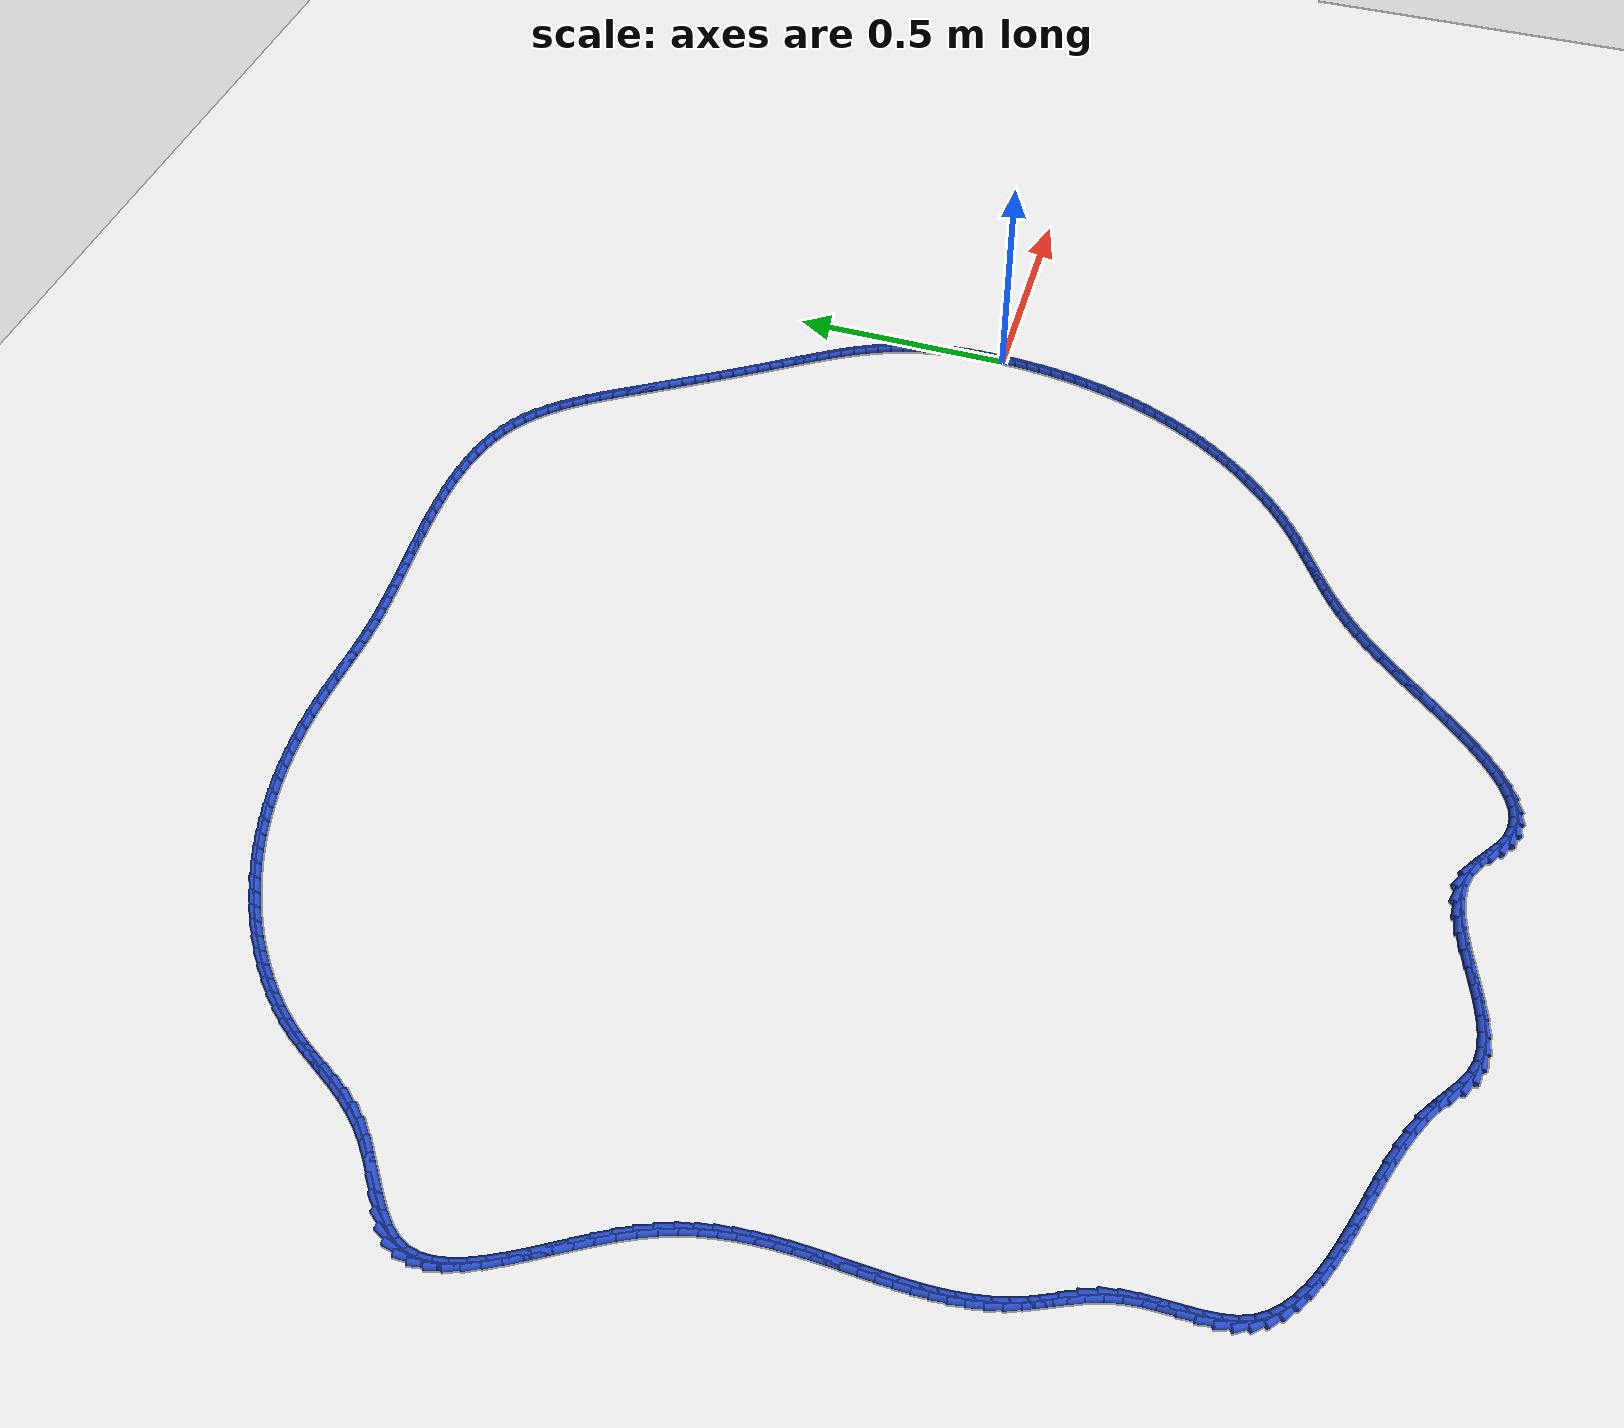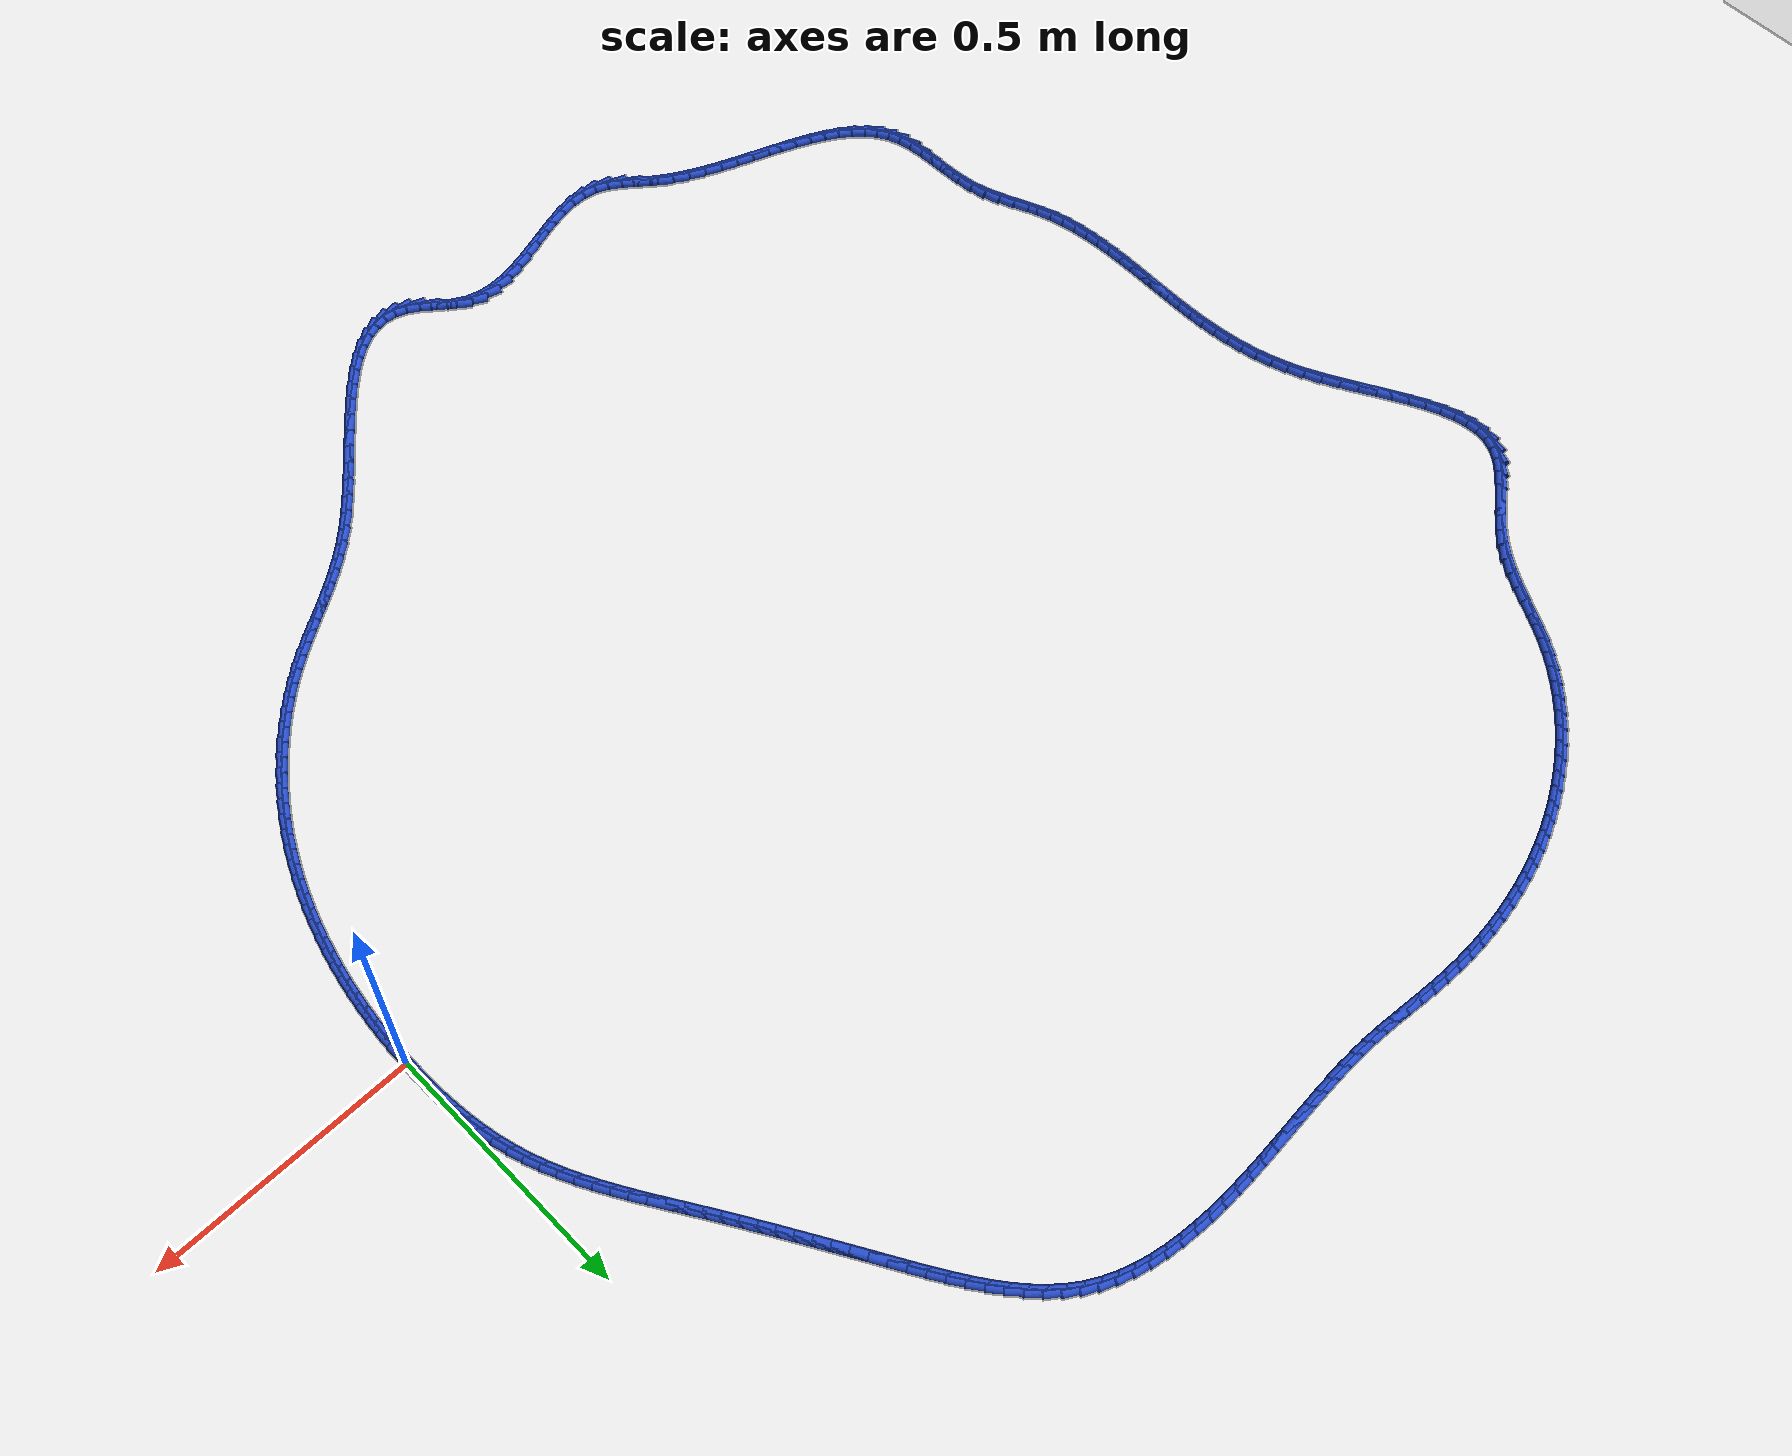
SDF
<sdf version="1.6">
 <world name="default">
  <light name="sun" type="directional">
   <pose>0 0 10 0 -0 0</pose>
   <diffuse>0.8 0.8 0.8 1</diffuse>
   <specular>0.2 0.2 0.2 1</specular>
   <attenuation>
    <range>1000</range>
    <constant>0.9</constant>
    <linear>0.01</linear>
    <quadratic>0.001</quadratic>
   </attenuation>
   <direction>-0.5 0.1 -0.9</direction>
  </light>
  <model name="ground_plane">
   <static>1</static>
   <link name="link">
    <collision name="collision">
     <geometry><plane><normal>0 0 1</normal><size>100 100</size></plane></geometry>
     <surface><friction><ode><mu>100</mu><mu2>50</mu2></ode></friction></surface>
    </collision>
    <visual name="visual">
     <cast_shadows>0</cast_shadows>
     <geometry><plane><normal>0 0 1</normal><size>100 100</size></plane></geometry>
     <material>
      <script><uri>file://media/materials/scripts/gazebo.material</uri><name>Gazebo/WhiteGlow</name></script>
     </material>
    </visual>
   </link>
  </model>
  <gravity>0 0 -9.8</gravity>
  <magnetic_field>6e-06 2.3e-05 -4.2e-05</magnetic_field>
  <atmosphere type="adiabatic"/>
  <physics name="default_physics" default="0" type="ode">
   <max_step_size>0.001</max_step_size>
   <real_time_factor>1</real_time_factor>
   <real_time_update_rate>1000</real_time_update_rate>
  </physics>
  <scene><ambient>0.4 0.4 0.4 1</ambient><background>0.7 0.7 0.7 1</background><shadows>1</shadows></scene>
  <spherical_coordinates>
   <surface_model>EARTH_WGS84</surface_model>
   <latitude_deg>0</latitude_deg>
   <longitude_deg>0</longitude_deg>
   <elevation>0</elevation>
   <heading_deg>0</heading_deg>
  </spherical_coordinates>
  <model name="line">
   <link name="link_0">
    <pose>-7.37257477290143e-18 -6.938893903907228e-18 0.01 0 1.57 1.5674022319807317</pose>
    <collision name="collision">
     <geometry><cylinder><radius>0.01</radius><length>0.08</length></cylinder></geometry>
    </collision>
    <visual name="visual">
     <material>
      <script><name>Gazebo/Blue</name><uri>file://media/materials/scripts/gazebo.material</uri></script>
     </material>
     <geometry><cylinder><radius>0.01</radius><length>0.08</length></cylinder></geometry>
    </visual>
   </link>
   <link name="link_1">
    <pose>0.00010328172378574896 0.03042971185034169 0.01 0 1.57 -1.5463053639427928</pose>
    <collision name="collision">
     <geometry><cylinder><radius>0.01</radius><length>0.08</length></cylinder></geometry>
    </collision>
    <visual name="visual">
     <material>
      <script><name>Gazebo/Blue</name><uri>file://media/materials/scripts/gazebo.material</uri></script>
     </material>
     <geometry><cylinder><radius>0.01</radius><length>0.08</length></cylinder></geometry>
    </visual>
   </link>
   <link name="link_2">
    <pose>-0.0006423701465075508 0.060869624987475605 0.01 0 1.57 -1.515353460619935</pose>
    <collision name="collision">
     <geometry><cylinder><radius>0.01</radius><length>0.08</length></cylinder></geometry>
    </collision>
    <visual name="visual">
     <material>
      <script><name>Gazebo/Blue</name><uri>file://media/materials/scripts/gazebo.material</uri></script>
     </material>
     <geometry><cylinder><radius>0.01</radius><length>0.08</length></cylinder></geometry>
    </visual>
   </link>
   <link name="link_3">
    <pose>-0.0023283620806781656 0.09124799764926991 0.01 0 1.57 -1.481179829045575</pose>
    <collision name="collision">
     <geometry><cylinder><radius>0.01</radius><length>0.08</length></cylinder></geometry>
    </collision>
    <visual name="visual">
     <material>
      <script><name>Gazebo/Blue</name><uri>file://media/materials/scripts/gazebo.material</uri></script>
     </material>
     <geometry><cylinder><radius>0.01</radius><length>0.08</length></cylinder></geometry>
    </visual>
   </link>
   <link name="link_4">
    <pose>-0.005046100548524349 0.12149308807359267 0.01 0 1.57 -1.4436273597365452</pose>
    <collision name="collision">
     <geometry><cylinder><radius>0.01</radius><length>0.08</length></cylinder></geometry>
    </collision>
    <visual name="visual">
     <material>
      <script><name>Gazebo/Blue</name><uri>file://media/materials/scripts/gazebo.material</uri></script>
     </material>
     <geometry><cylinder><radius>0.01</radius><length>0.08</length></cylinder></geometry>
    </visual>
   </link>
   <link name="link_5">
    <pose>-0.008886992019844362 0.151533154498312 0.01 0 1.57 -1.402546920274872</pose>
    <collision name="collision">
     <geometry><cylinder><radius>0.01</radius><length>0.08</length></cylinder></geometry>
    </collision>
    <visual name="visual">
     <material>
      <script><name>Gazebo/Blue</name><uri>file://media/materials/scripts/gazebo.material</uri></script>
     </material>
     <geometry><cylinder><radius>0.01</radius><length>0.08</length></cylinder></geometry>
    </visual>
   </link>
   <link name="link_6">
    <pose>-0.01394244296443647 0.18129645516129603 0.01 0 1.57 -1.3578105071537598</pose>
    <collision name="collision">
     <geometry><cylinder><radius>0.01</radius><length>0.08</length></cylinder></geometry>
    </collision>
    <visual name="visual">
     <material>
      <script><name>Gazebo/Blue</name><uri>file://media/materials/scripts/gazebo.material</uri></script>
     </material>
     <geometry><cylinder><radius>0.01</radius><length>0.08</length></cylinder></geometry>
    </visual>
   </link>
   <link name="link_7">
    <pose>-0.020303859852098916 0.21071124830041288 0.01 0 1.57 -1.3093276165098042</pose>
    <collision name="collision">
     <geometry><cylinder><radius>0.01</radius><length>0.08</length></cylinder></geometry>
    </collision>
    <visual name="visual">
     <material>
      <script><name>Gazebo/Blue</name><uri>file://media/materials/scripts/gazebo.material</uri></script>
     </material>
     <geometry><cylinder><radius>0.01</radius><length>0.08</length></cylinder></geometry>
    </visual>
   </link>
   <link name="link_8">
    <pose>-0.028062649152629963 0.23970579215353066 0.01 0 1.57 -1.2571251343741232</pose>
    <collision name="collision">
     <geometry><cylinder><radius>0.01</radius><length>0.08</length></cylinder></geometry>
    </collision>
    <visual name="visual">
     <material>
      <script><name>Gazebo/Blue</name><uri>file://media/materials/scripts/gazebo.material</uri></script>
     </material>
     <geometry><cylinder><radius>0.01</radius><length>0.08</length></cylinder></geometry>
    </visual>
   </link>
   <link name="link_9">
    <pose>-0.037308552403289105 0.26820908481968486 0.01 0 1.57 -1.204940926215308</pose>
    <collision name="collision">
     <geometry><cylinder><radius>0.01</radius><length>0.08</length></cylinder></geometry>
    </collision>
    <visual name="visual">
     <material>
      <script><name>Gazebo/Blue</name><uri>file://media/materials/scripts/gazebo.material</uri></script>
     </material>
     <geometry><cylinder><radius>0.01</radius><length>0.08</length></cylinder></geometry>
    </visual>
   </link>
   <link name="link_10">
    <pose>-0.048030074452251305 0.29619511186330744 0.01 0 1.57 -1.1586576392292973</pose>
    <collision name="collision">
     <geometry><cylinder><radius>0.01</radius><length>0.08</length></cylinder></geometry>
    </collision>
    <visual name="visual">
     <material>
      <script><name>Gazebo/Blue</name><uri>file://media/materials/scripts/gazebo.material</uri></script>
     </material>
     <geometry><cylinder><radius>0.01</radius><length>0.08</length></cylinder></geometry>
    </visual>
   </link>
   <link name="link_11">
    <pose>-0.06005802746195553 0.32370793417731925 0.01 0 1.57 -1.1188317549096656</pose>
    <collision name="collision">
     <geometry><cylinder><radius>0.01</radius><length>0.08</length></cylinder></geometry>
    </collision>
    <visual name="visual">
     <material>
      <script><name>Gazebo/Blue</name><uri>file://media/materials/scripts/gazebo.material</uri></script>
     </material>
     <geometry><cylinder><radius>0.01</radius><length>0.08</length></cylinder></geometry>
    </visual>
   </link>
   <link name="link_12">
    <pose>-0.07320956755038621 0.35079768111492915 0.01 0 1.57 -1.0854157992072404</pose>
    <collision name="collision">
     <geometry><cylinder><radius>0.01</radius><length>0.08</length></cylinder></geometry>
    </collision>
    <visual name="visual">
     <material>
      <script><name>Gazebo/Blue</name><uri>file://media/materials/scripts/gazebo.material</uri></script>
     </material>
     <geometry><cylinder><radius>0.01</radius><length>0.08</length></cylinder></geometry>
    </visual>
   </link>
   <link name="link_13">
    <pose>-0.08730185083552774 0.3775144820293458 0.01 0 1.57 -1.0583042262396472</pose>
    <collision name="collision">
     <geometry><cylinder><radius>0.01</radius><length>0.08</length></cylinder></geometry>
    </collision>
    <visual name="visual">
     <material>
      <script><name>Gazebo/Blue</name><uri>file://media/materials/scripts/gazebo.material</uri></script>
     </material>
     <geometry><cylinder><radius>0.01</radius><length>0.08</length></cylinder></geometry>
    </visual>
   </link>
   <link name="link_14">
    <pose>-0.1021520334353646 0.40390846627377774 0.01 0 1.57 -1.0373740282187012</pose>
    <collision name="collision">
     <geometry><cylinder><radius>0.01</radius><length>0.08</length></cylinder></geometry>
    </collision>
    <visual name="visual">
     <material>
      <script><name>Gazebo/Blue</name><uri>file://media/materials/scripts/gazebo.material</uri></script>
     </material>
     <geometry><cylinder><radius>0.01</radius><length>0.08</length></cylinder></geometry>
    </visual>
   </link>
   <link name="link_15">
    <pose>-0.11757727146788118 0.4300297632014336 0.01 0 1.57 -1.0225156596896658</pose>
    <collision name="collision">
     <geometry><cylinder><radius>0.01</radius><length>0.08</length></cylinder></geometry>
    </collision>
    <visual name="visual">
     <material>
      <script><name>Gazebo/Blue</name><uri>file://media/materials/scripts/gazebo.material</uri></script>
     </material>
     <geometry><cylinder><radius>0.01</radius><length>0.08</length></cylinder></geometry>
    </visual>
   </link>
   <link name="link_16">
    <pose>-0.13339472105106187 0.45592850216552205 0.01 0 1.57 -1.0136553831200168</pose>
    <collision name="collision">
     <geometry><cylinder><radius>0.01</radius><length>0.08</length></cylinder></geometry>
    </collision>
    <visual name="visual">
     <material>
      <script><name>Gazebo/Blue</name><uri>file://media/materials/scripts/gazebo.material</uri></script>
     </material>
     <geometry><cylinder><radius>0.01</radius><length>0.08</length></cylinder></geometry>
    </visual>
   </link>
   <link name="link_17">
    <pose>-0.14942153830289126 0.481654812519252 0.01 0 1.57 -1.0107705846912403</pose>
    <collision name="collision">
     <geometry><cylinder><radius>0.01</radius><length>0.08</length></cylinder></geometry>
    </collision>
    <visual name="visual">
     <material>
      <script><name>Gazebo/Blue</name><uri>file://media/materials/scripts/gazebo.material</uri></script>
     </material>
     <geometry><cylinder><radius>0.01</radius><length>0.08</length></cylinder></geometry>
    </visual>
   </link>
   <link name="link_18">
    <pose>-0.16547487934135363 0.5072588236158317 0.01 0 1.57 -1.0137283619796218</pose>
    <collision name="collision">
     <geometry><cylinder><radius>0.01</radius><length>0.08</length></cylinder></geometry>
    </collision>
    <visual name="visual">
     <material>
      <script><name>Gazebo/Blue</name><uri>file://media/materials/scripts/gazebo.material</uri></script>
     </material>
     <geometry><cylinder><radius>0.01</radius><length>0.08</length></cylinder></geometry>
    </visual>
   </link>
   <link name="link_19">
    <pose>-0.18137769046557403 0.5327902303137512 0.01 0 1.57 -1.019291092657098</pose>
    <collision name="collision">
     <geometry><cylinder><radius>0.01</radius><length>0.08</length></cylinder></geometry>
    </collision>
    <visual name="visual">
     <material>
      <script><name>Gazebo/Blue</name><uri>file://media/materials/scripts/gazebo.material</uri></script>
     </material>
     <geometry><cylinder><radius>0.01</radius><length>0.08</length></cylinder></geometry>
    </visual>
   </link>
   <link name="link_20">
    <pose>-0.19706479659043677 0.5582903321093274 0.01 0 1.57 -1.024461029910032</pose>
    <collision name="collision">
     <geometry><cylinder><radius>0.01</radius><length>0.08</length></cylinder></geometry>
    </collision>
    <visual name="visual">
     <material>
      <script><name>Gazebo/Blue</name><uri>file://media/materials/scripts/gazebo.material</uri></script>
     </material>
     <geometry><cylinder><radius>0.01</radius><length>0.08</length></cylinder></geometry>
    </visual>
   </link>
   <link name="link_21">
    <pose>-0.21257221174297006 0.5837928352761822 0.01 0 1.57 -1.0290999874890407</pose>
    <collision name="collision">
     <geometry><cylinder><radius>0.01</radius><length>0.08</length></cylinder></geometry>
    </collision>
    <visual name="visual">
     <material>
      <script><name>Gazebo/Blue</name><uri>file://media/materials/scripts/gazebo.material</uri></script>
     </material>
     <geometry><cylinder><radius>0.01</radius><length>0.08</length></cylinder></geometry>
    </visual>
   </link>
   <link name="link_22">
    <pose>-0.22793959546960188 0.6093311725284594 0.01 0 1.57 -1.0331825921077555</pose>
    <collision name="collision">
     <geometry><cylinder><radius>0.01</radius><length>0.08</length></cylinder></geometry>
    </collision>
    <visual name="visual">
     <material>
      <script><name>Gazebo/Blue</name><uri>file://media/materials/scripts/gazebo.material</uri></script>
     </material>
     <geometry><cylinder><radius>0.01</radius><length>0.08</length></cylinder></geometry>
    </visual>
   </link>
   <link name="link_23">
    <pose>-0.24320660731676025 0.6349387765803034 0.01 0 1.57 -1.0366890266519224</pose>
    <collision name="collision">
     <geometry><cylinder><radius>0.01</radius><length>0.08</length></cylinder></geometry>
    </collision>
    <visual name="visual">
     <material>
      <script><name>Gazebo/Blue</name><uri>file://media/materials/scripts/gazebo.material</uri></script>
     </material>
     <geometry><cylinder><radius>0.01</radius><length>0.08</length></cylinder></geometry>
    </visual>
   </link>
   <link name="link_24">
    <pose>-0.258412906830873 0.6606490801458582 0.01 0 1.57 -1.0396053130117529</pose>
    <collision name="collision">
     <geometry><cylinder><radius>0.01</radius><length>0.08</length></cylinder></geometry>
    </collision>
    <visual name="visual">
     <material>
      <script><name>Gazebo/Blue</name><uri>file://media/materials/scripts/gazebo.material</uri></script>
     </material>
     <geometry><cylinder><radius>0.01</radius><length>0.08</length></cylinder></geometry>
    </visual>
   </link>
   <link name="link_25">
    <pose>-0.2735981535583682 0.6864955159392684 0.01 0 1.57 -1.04192345153611</pose>
    <collision name="collision">
     <geometry><cylinder><radius>0.01</radius><length>0.08</length></cylinder></geometry>
    </collision>
    <visual name="visual">
     <material>
      <script><name>Gazebo/Blue</name><uri>file://media/materials/scripts/gazebo.material</uri></script>
     </material>
     <geometry><cylinder><radius>0.01</radius><length>0.08</length></cylinder></geometry>
    </visual>
   </link>
   <link name="link_26">
    <pose>-0.28880200704567366 0.7125115166746774 0.01 0 1.57 -1.0436414164426133</pose>
    <collision name="collision">
     <geometry><cylinder><radius>0.01</radius><length>0.08</length></cylinder></geometry>
    </collision>
    <visual name="visual">
     <material>
      <script><name>Gazebo/Blue</name><uri>file://media/materials/scripts/gazebo.material</uri></script>
     </material>
     <geometry><cylinder><radius>0.01</radius><length>0.08</length></cylinder></geometry>
    </visual>
   </link>
   <link name="link_27">
    <pose>-0.30406412683921735 0.7387305150662298 0.01 0 1.57 -1.0447630125856138</pose>
    <collision name="collision">
     <geometry><cylinder><radius>0.01</radius><length>0.08</length></cylinder></geometry>
    </collision>
    <visual name="visual">
     <material>
      <script><name>Gazebo/Blue</name><uri>file://media/materials/scripts/gazebo.material</uri></script>
     </material>
     <geometry><cylinder><radius>0.01</radius><length>0.08</length></cylinder></geometry>
    </visual>
   </link>
   <link name="link_28">
    <pose>-0.3194241724854271 0.7651859438280693 0.01 0 1.57 -1.0452976043324436</pose>
    <collision name="collision">
     <geometry><cylinder><radius>0.01</radius><length>0.08</length></cylinder></geometry>
    </collision>
    <visual name="visual">
     <material>
      <script><name>Gazebo/Blue</name><uri>file://media/materials/scripts/gazebo.material</uri></script>
     </material>
     <geometry><cylinder><radius>0.01</radius><length>0.08</length></cylinder></geometry>
    </visual>
   </link>
   <link name="link_29">
    <pose>-0.334921803531928 0.7919112356701343 0.01 0 1.57 -1.043949242646931</pose>
    <collision name="collision">
     <geometry><cylinder><radius>0.01</radius><length>0.08</length></cylinder></geometry>
    </collision>
    <visual name="visual">
     <material>
      <script><name>Gazebo/Blue</name><uri>file://media/materials/scripts/gazebo.material</uri></script>
     </material>
     <geometry><cylinder><radius>0.01</radius><length>0.08</length></cylinder></geometry>
    </visual>
   </link>
   <link name="link_30">
    <pose>-0.3506122394375096 0.8188851382346258 0.01 0 1.57 -1.0356049996372712</pose>
    <collision name="collision">
     <geometry><cylinder><radius>0.01</radius><length>0.08</length></cylinder></geometry>
    </collision>
    <visual name="visual">
     <material>
      <script><name>Gazebo/Blue</name><uri>file://media/materials/scripts/gazebo.material</uri></script>
     </material>
     <geometry><cylinder><radius>0.01</radius><length>0.08</length></cylinder></geometry>
    </visual>
   </link>
   <link name="link_31">
    <pose>-0.3666121469347485 0.8458704436680093 0.01 0 1.57 -1.0189613494072602</pose>
    <collision name="collision">
     <geometry><cylinder><radius>0.01</radius><length>0.08</length></cylinder></geometry>
    </collision>
    <visual name="visual">
     <material>
      <script><name>Gazebo/Blue</name><uri>file://media/materials/scripts/gazebo.material</uri></script>
     </material>
     <geometry><cylinder><radius>0.01</radius><length>0.08</length></cylinder></geometry>
    </visual>
   </link>
   <link name="link_32">
    <pose>-0.3830533589974266 0.8725766425960131 0.01 0 1.57 -0.9937336484632711</pose>
    <collision name="collision">
     <geometry><cylinder><radius>0.01</radius><length>0.08</length></cylinder></geometry>
    </collision>
    <visual name="visual">
     <material>
      <script><name>Gazebo/Blue</name><uri>file://media/materials/scripts/gazebo.material</uri></script>
     </material>
     <geometry><cylinder><radius>0.01</radius><length>0.08</length></cylinder></geometry>
    </visual>
   </link>
   <link name="link_33">
    <pose>-0.4000677085993259 0.8987132256443665 0.01 0 1.57 -0.9593856578627199</pose>
    <collision name="collision">
     <geometry><cylinder><radius>0.01</radius><length>0.08</length></cylinder></geometry>
    </collision>
    <visual name="visual">
     <material>
      <script><name>Gazebo/Blue</name><uri>file://media/materials/scripts/gazebo.material</uri></script>
     </material>
     <geometry><cylinder><radius>0.01</radius><length>0.08</length></cylinder></geometry>
    </visual>
   </link>
   <link name="link_34">
    <pose>-0.4177870287142279 0.9239896834387973 0.01 0 1.57 -0.9151580423322914</pose>
    <collision name="collision">
     <geometry><cylinder><radius>0.01</radius><length>0.08</length></cylinder></geometry>
    </collision>
    <visual name="visual">
     <material>
      <script><name>Gazebo/Blue</name><uri>file://media/materials/scripts/gazebo.material</uri></script>
     </material>
     <geometry><cylinder><radius>0.01</radius><length>0.08</length></cylinder></geometry>
    </visual>
   </link>
   <link name="link_35">
    <pose>-0.436343152315915 0.9481155066050351 0.01 0 1.57 -0.8601216312061593</pose>
    <collision name="collision">
     <geometry><cylinder><radius>0.01</radius><length>0.08</length></cylinder></geometry>
    </collision>
    <visual name="visual">
     <material>
      <script><name>Gazebo/Blue</name><uri>file://media/materials/scripts/gazebo.material</uri></script>
     </material>
     <geometry><cylinder><radius>0.01</radius><length>0.08</length></cylinder></geometry>
    </visual>
   </link>
   <link name="link_36">
    <pose>-0.4558679123781686 0.970800185768808 0.01 0 1.57 -0.7932818395417996</pose>
    <collision name="collision">
     <geometry><cylinder><radius>0.01</radius><length>0.08</length></cylinder></geometry>
    </collision>
    <visual name="visual">
     <material>
      <script><name>Gazebo/Blue</name><uri>file://media/materials/scripts/gazebo.material</uri></script>
     </material>
     <geometry><cylinder><radius>0.01</radius><length>0.08</length></cylinder></geometry>
    </visual>
   </link>
   <link name="link_37">
    <pose>-0.4764931418747708 0.991753211555845 0.01 0 1.57 -0.713768432492929</pose>
    <collision name="collision">
     <geometry><cylinder><radius>0.01</radius><length>0.08</length></cylinder></geometry>
    </collision>
    <visual name="visual">
     <material>
      <script><name>Gazebo/Blue</name><uri>file://media/materials/scripts/gazebo.material</uri></script>
     </material>
     <geometry><cylinder><radius>0.01</radius><length>0.08</length></cylinder></geometry>
    </visual>
   </link>
   <link name="link_38">
    <pose>-0.4983506737795034 1.0106840745918744 0.01 0 1.57 -0.6211822560639534</pose>
    <collision name="collision">
     <geometry><cylinder><radius>0.01</radius><length>0.08</length></cylinder></geometry>
    </collision>
    <visual name="visual">
     <material>
      <script><name>Gazebo/Blue</name><uri>file://media/materials/scripts/gazebo.material</uri></script>
     </material>
     <geometry><cylinder><radius>0.01</radius><length>0.08</length></cylinder></geometry>
    </visual>
   </link>
   <link name="link_39">
    <pose>-0.5215717670807007 1.0273033025566032 0.01 0 1.57 -0.5216711507332075</pose>
    <collision name="collision">
     <geometry><cylinder><radius>0.01</radius><length>0.08</length></cylinder></geometry>
    </collision>
    <visual name="visual">
     <material>
      <script><name>Gazebo/Blue</name><uri>file://media/materials/scripts/gazebo.material</uri></script>
     </material>
     <geometry><cylinder><radius>0.01</radius><length>0.08</length></cylinder></geometry>
    </visual>
   </link>
   <link name="link_40">
    <pose>-0.5462086709093774 1.0414641749837474 0.01 0 1.57 -0.42819718281324015</pose>
    <collision name="collision">
     <geometry><cylinder><radius>0.01</radius><length>0.08</length></cylinder></geometry>
    </collision>
    <visual name="visual">
     <material>
      <script><name>Gazebo/Blue</name><uri>file://media/materials/scripts/gazebo.material</uri></script>
     </material>
     <geometry><cylinder><radius>0.01</radius><length>0.08</length></cylinder></geometry>
    </visual>
   </link>
   <link name="link_41">
    <pose>-0.5721547557172986 1.0533070270579885 0.01 0 1.57 -0.3433644135498441</pose>
    <collision name="collision">
     <geometry><cylinder><radius>0.01</radius><length>0.08</length></cylinder></geometry>
    </collision>
    <visual name="visual">
     <material>
      <script><name>Gazebo/Blue</name><uri>file://media/materials/scripts/gazebo.material</uri></script>
     </material>
     <geometry><cylinder><radius>0.01</radius><length>0.08</length></cylinder></geometry>
    </visual>
   </link>
   <link name="link_42">
    <pose>-0.5992843564667999 1.0630065865259022 0.01 0 1.57 -0.2676881430412302</pose>
    <collision name="collision">
     <geometry><cylinder><radius>0.01</radius><length>0.08</length></cylinder></geometry>
    </collision>
    <visual name="visual">
     <material>
      <script><name>Gazebo/Blue</name><uri>file://media/materials/scripts/gazebo.material</uri></script>
     </material>
     <geometry><cylinder><radius>0.01</radius><length>0.08</length></cylinder></geometry>
    </visual>
   </link>
   <link name="link_43">
    <pose>-0.627471808120217 1.0707375811340618 0.01 0 1.57 -0.20113163423391656</pose>
    <collision name="collision">
     <geometry><cylinder><radius>0.01</radius><length>0.08</length></cylinder></geometry>
    </collision>
    <visual name="visual">
     <material>
      <script><name>Gazebo/Blue</name><uri>file://media/materials/scripts/gazebo.material</uri></script>
     </material>
     <geometry><cylinder><radius>0.01</radius><length>0.08</length></cylinder></geometry>
    </visual>
   </link>
   <link name="link_44">
    <pose>-0.6565914456398854 1.0766747386290427 0.01 0 1.57 -0.1433010617571937</pose>
    <collision name="collision">
     <geometry><cylinder><radius>0.01</radius><length>0.08</length></cylinder></geometry>
    </collision>
    <visual name="visual">
     <material>
      <script><name>Gazebo/Blue</name><uri>file://media/materials/scripts/gazebo.material</uri></script>
     </material>
     <geometry><cylinder><radius>0.01</radius><length>0.08</length></cylinder></geometry>
    </visual>
   </link>
   <link name="link_45">
    <pose>-0.6865176039881408 1.08099278675742 0.01 0 1.57 -0.09361471595546612</pose>
    <collision name="collision">
     <geometry><cylinder><radius>0.01</radius><length>0.08</length></cylinder></geometry>
    </collision>
    <visual name="visual">
     <material>
      <script><name>Gazebo/Blue</name><uri>file://media/materials/scripts/gazebo.material</uri></script>
     </material>
     <geometry><cylinder><radius>0.01</radius><length>0.08</length></cylinder></geometry>
    </visual>
   </link>
   <link name="link_46">
    <pose>-0.7171246181273184 1.0838664532657676 0.01 0 1.57 -0.0514276282113222</pose>
    <collision name="collision">
     <geometry><cylinder><radius>0.01</radius><length>0.08</length></cylinder></geometry>
    </collision>
    <visual name="visual">
     <material>
      <script><name>Gazebo/Blue</name><uri>file://media/materials/scripts/gazebo.material</uri></script>
     </material>
     <geometry><cylinder><radius>0.01</radius><length>0.08</length></cylinder></geometry>
    </visual>
   </link>
   <link name="link_47">
    <pose>-0.7482868230197548 1.0854704659006609 0.01 0 1.57 -0.016113154891228592</pose>
    <collision name="collision">
     <geometry><cylinder><radius>0.01</radius><length>0.08</length></cylinder></geometry>
    </collision>
    <visual name="visual">
     <material>
      <script><name>Gazebo/Blue</name><uri>file://media/materials/scripts/gazebo.material</uri></script>
     </material>
     <geometry><cylinder><radius>0.01</radius><length>0.08</length></cylinder></geometry>
    </visual>
   </link>
   <link name="link_48">
    <pose>-0.7798785536277849 1.0859795524086742 0.01 0 1.57 0.012888587150228203</pose>
    <collision name="collision">
     <geometry><cylinder><radius>0.01</radius><length>0.08</length></cylinder></geometry>
    </collision>
    <visual name="visual">
     <material>
      <script><name>Gazebo/Blue</name><uri>file://media/materials/scripts/gazebo.material</uri></script>
     </material>
     <geometry><cylinder><radius>0.01</radius><length>0.08</length></cylinder></geometry>
    </visual>
   </link>
   <link name="link_49">
    <pose>-0.8117741449137442 1.0855684405363824 0.01 0 1.57 0.03604443676746142</pose>
    <collision name="collision">
     <geometry><cylinder><radius>0.01</radius><length>0.08</length></cylinder></geometry>
    </collision>
    <visual name="visual">
     <material>
      <script><name>Gazebo/Blue</name><uri>file://media/materials/scripts/gazebo.material</uri></script>
     </material>
     <geometry><cylinder><radius>0.01</radius><length>0.08</length></cylinder></geometry>
    </visual>
   </link>
   <link name="link_50">
    <pose>-0.843847931839969 1.08441185803036 0.01 0 1.57 0.05371495783498905</pose>
    <collision name="collision">
     <geometry><cylinder><radius>0.01</radius><length>0.08</length></cylinder></geometry>
    </collision>
    <visual name="visual">
     <material>
      <script><name>Gazebo/Blue</name><uri>file://media/materials/scripts/gazebo.material</uri></script>
     </material>
     <geometry><cylinder><radius>0.01</radius><length>0.08</length></cylinder></geometry>
    </visual>
   </link>
   <link name="link_51">
    <pose>-0.8759742493687943 1.0826845326371823 0.01 0 1.57 0.06614764978109962</pose>
    <collision name="collision">
     <geometry><cylinder><radius>0.01</radius><length>0.08</length></cylinder></geometry>
    </collision>
    <visual name="visual">
     <material>
      <script><name>Gazebo/Blue</name><uri>file://media/materials/scripts/gazebo.material</uri></script>
     </material>
     <geometry><cylinder><radius>0.01</radius><length>0.08</length></cylinder></geometry>
    </visual>
   </link>
   <link name="link_52">
    <pose>-0.9080274324625561 1.0805611921034233 0.01 0 1.57 0.07347207077993372</pose>
    <collision name="collision">
     <geometry><cylinder><radius>0.01</radius><length>0.08</length></cylinder></geometry>
    </collision>
    <visual name="visual">
     <material>
      <script><name>Gazebo/Blue</name><uri>file://media/materials/scripts/gazebo.material</uri></script>
     </material>
     <geometry><cylinder><radius>0.01</radius><length>0.08</length></cylinder></geometry>
    </visual>
   </link>
   <link name="link_53">
    <pose>-0.9398818160835898 1.0782165641756585 0.01 0 1.57 0.0756937882469786</pose>
    <collision name="collision">
     <geometry><cylinder><radius>0.01</radius><length>0.08</length></cylinder></geometry>
    </collision>
    <visual name="visual">
     <material>
      <script><name>Gazebo/Blue</name><uri>file://media/materials/scripts/gazebo.material</uri></script>
     </material>
     <geometry><cylinder><radius>0.01</radius><length>0.08</length></cylinder></geometry>
    </visual>
   </link>
   <link name="link_54">
    <pose>-0.9714117351942313 1.0758253766004617 0.01 0 1.57 0.07268902405615534</pose>
    <collision name="collision">
     <geometry><cylinder><radius>0.01</radius><length>0.08</length></cylinder></geometry>
    </collision>
    <visual name="visual">
     <material>
      <script><name>Gazebo/Blue</name><uri>file://media/materials/scripts/gazebo.material</uri></script>
     </material>
     <geometry><cylinder><radius>0.01</radius><length>0.08</length></cylinder></geometry>
    </visual>
   </link>
   <link name="link_55">
    <pose>-1.0024930394067058 1.0735621194064116 0.01 0 1.57 0.06445204321105084</pose>
    <collision name="collision">
     <geometry><cylinder><radius>0.01</radius><length>0.08</length></cylinder></geometry>
    </collision>
    <visual name="visual">
     <material>
      <script><name>Gazebo/Blue</name><uri>file://media/materials/scripts/gazebo.material</uri></script>
     </material>
     <geometry><cylinder><radius>0.01</radius><length>0.08</length></cylinder></geometry>
    </visual>
   </link>
   <link name="link_56">
    <pose>-1.0330906236823774 1.0715873073251114 0.01 0 1.57 0.05116537946690907</pose>
    <collision name="collision">
     <geometry><cylinder><radius>0.01</radius><length>0.08</length></cylinder></geometry>
    </collision>
    <visual name="visual">
     <material>
      <script><name>Gazebo/Blue</name><uri>file://media/materials/scripts/gazebo.material</uri></script>
     </material>
     <geometry><cylinder><radius>0.01</radius><length>0.08</length></cylinder></geometry>
    </visual>
   </link>
   <link name="link_57">
    <pose>-1.0633063591276122 1.0700399572522505 0.01 0 1.57 0.03280245692929859</pose>
    <collision name="collision">
     <geometry><cylinder><radius>0.01</radius><length>0.08</length></cylinder></geometry>
    </collision>
    <visual name="visual">
     <material>
      <script><name>Gazebo/Blue</name><uri>file://media/materials/scripts/gazebo.material</uri></script>
     </material>
     <geometry><cylinder><radius>0.01</radius><length>0.08</length></cylinder></geometry>
    </visual>
   </link>
   <link name="link_58">
    <pose>-1.0932537785456033 1.0690572558287317 0.01 0 1.57 0.00942708833165252</pose>
    <collision name="collision">
     <geometry><cylinder><radius>0.01</radius><length>0.08</length></cylinder></geometry>
    </collision>
    <visual name="visual">
     <material>
      <script><name>Gazebo/Blue</name><uri>file://media/materials/scripts/gazebo.material</uri></script>
     </material>
     <geometry><cylinder><radius>0.01</radius><length>0.08</length></cylinder></geometry>
    </visual>
   </link>
   <link name="link_59">
    <pose>-1.1230464147395454 1.0687763896954587 0.01 0 1.57 -0.018758464988508604</pose>
    <collision name="collision">
     <geometry><cylinder><radius>0.01</radius><length>0.08</length></cylinder></geometry>
    </collision>
    <visual name="visual">
     <material>
      <script><name>Gazebo/Blue</name><uri>file://media/materials/scripts/gazebo.material</uri></script>
     </material>
     <geometry><cylinder><radius>0.01</radius><length>0.08</length></cylinder></geometry>
    </visual>
   </link>
   <link name="link_60">
    <pose>-1.1527978005126305 1.0693345454933343 0.01 0 1.57 -0.05000343111768362</pose>
    <collision name="collision">
     <geometry><cylinder><radius>0.01</radius><length>0.08</length></cylinder></geometry>
    </collision>
    <visual name="visual">
     <material>
      <script><name>Gazebo/Blue</name><uri>file://media/materials/scripts/gazebo.material</uri></script>
     </material>
     <geometry><cylinder><radius>0.01</radius><length>0.08</length></cylinder></geometry>
    </visual>
   </link>
   <link name="link_61">
    <pose>-1.1826110905676024 1.070826556009064 0.01 0 1.57 -0.07393618287074608</pose>
    <collision name="collision">
     <geometry><cylinder><radius>0.01</radius><length>0.08</length></cylinder></geometry>
    </collision>
    <visual name="visual">
     <material>
      <script><name>Gazebo/Blue</name><uri>file://media/materials/scripts/gazebo.material</uri></script>
     </material>
     <geometry><cylinder><radius>0.01</radius><length>0.08</length></cylinder></geometry>
    </visual>
   </link>
   <link name="link_62">
    <pose>-1.2125145294514361 1.073041539719667 0.01 0 1.57 -0.08624608757727836</pose>
    <collision name="collision">
     <geometry><cylinder><radius>0.01</radius><length>0.08</length></cylinder></geometry>
    </collision>
    <visual name="visual">
     <material>
      <script><name>Gazebo/Blue</name><uri>file://media/materials/scripts/gazebo.material</uri></script>
     </material>
     <geometry><cylinder><radius>0.01</radius><length>0.08</length></cylinder></geometry>
    </visual>
   </link>
   <link name="link_63">
    <pose>-1.2425034748049302 1.0756344010197465 0.01 0 1.57 -0.0870787682468536</pose>
    <collision name="collision">
     <geometry><cylinder><radius>0.01</radius><length>0.08</length></cylinder></geometry>
    </collision>
    <visual name="visual">
     <material>
      <script><name>Gazebo/Blue</name><uri>file://media/materials/scripts/gazebo.material</uri></script>
     </material>
     <geometry><cylinder><radius>0.01</radius><length>0.08</length></cylinder></geometry>
    </visual>
   </link>
   <link name="link_64">
    <pose>-1.272573143329235 1.0782594691179848 0.01 0 1.57 -0.076531521042552</pose>
    <collision name="collision">
     <geometry><cylinder><radius>0.01</radius><length>0.08</length></cylinder></geometry>
    </collision>
    <visual name="visual">
     <material>
      <script><name>Gazebo/Blue</name><uri>file://media/materials/scripts/gazebo.material</uri></script>
     </material>
     <geometry><cylinder><radius>0.01</radius><length>0.08</length></cylinder></geometry>
    </visual>
   </link>
   <link name="link_65">
    <pose>-1.3027187517255008 1.080571073223063 0.01 0 1.57 -0.05463274883324481</pose>
    <collision name="collision">
     <geometry><cylinder><radius>0.01</radius><length>0.08</length></cylinder></geometry>
    </collision>
    <visual name="visual">
     <material>
      <script><name>Gazebo/Blue</name><uri>file://media/materials/scripts/gazebo.material</uri></script>
     </material>
     <geometry><cylinder><radius>0.01</radius><length>0.08</length></cylinder></geometry>
    </visual>
   </link>
   <link name="link_66">
    <pose>-1.3329355166948793 1.0822235425436633 0.01 0 1.57 -0.022350645886211076</pose>
    <collision name="collision">
     <geometry><cylinder><radius>0.01</radius><length>0.08</length></cylinder></geometry>
    </collision>
    <visual name="visual">
     <material>
      <script><name>Gazebo/Blue</name><uri>file://media/materials/scripts/gazebo.material</uri></script>
     </material>
     <geometry><cylinder><radius>0.01</radius><length>0.08</length></cylinder></geometry>
    </visual>
   </link>
   <link name="link_67">
    <pose>-1.363214995582436 1.0829004211695339 0.01 0 1.57 0.013401554270666772</pose>
    <collision name="collision">
     <geometry><cylinder><radius>0.01</radius><length>0.08</length></cylinder></geometry>
    </collision>
    <visual name="visual">
     <material>
      <script><name>Gazebo/Blue</name><uri>file://media/materials/scripts/gazebo.material</uri></script>
     </material>
     <geometry><cylinder><radius>0.01</radius><length>0.08</length></cylinder></geometry>
    </visual>
   </link>
   <link name="link_68">
    <pose>-1.3935225702326146 1.0824942282451153 0.01 0 1.57 0.049670177782907304</pose>
    <collision name="collision">
     <geometry><cylinder><radius>0.01</radius><length>0.08</length></cylinder></geometry>
    </collision>
    <visual name="visual">
     <material>
      <script><name>Gazebo/Blue</name><uri>file://media/materials/scripts/gazebo.material</uri></script>
     </material>
     <geometry><cylinder><radius>0.01</radius><length>0.08</length></cylinder></geometry>
    </visual>
   </link>
   <link name="link_69">
    <pose>-1.423812222331684 1.080988497360439 0.01 0 1.57 0.08650983107773058</pose>
    <collision name="collision">
     <geometry><cylinder><radius>0.01</radius><length>0.08</length></cylinder></geometry>
    </collision>
    <visual name="visual">
     <material>
      <script><name>Gazebo/Blue</name><uri>file://media/materials/scripts/gazebo.material</uri></script>
     </material>
     <geometry><cylinder><radius>0.01</radius><length>0.08</length></cylinder></geometry>
    </visual>
   </link>
   <link name="link_70">
    <pose>-1.454037886530822 1.0783671376154902 0.01 0 1.57 0.12398317968585287</pose>
    <collision name="collision">
     <geometry><cylinder><radius>0.01</radius><length>0.08</length></cylinder></geometry>
    </collision>
    <visual name="visual">
     <material>
      <script><name>Gazebo/Blue</name><uri>file://media/materials/scripts/gazebo.material</uri></script>
     </material>
     <geometry><cylinder><radius>0.01</radius><length>0.08</length></cylinder></geometry>
    </visual>
   </link>
   <link name="link_71">
    <pose>-1.4841534974812054 1.0746140581102548 0.01 0 1.57 0.1621477234165601</pose>
    <collision name="collision">
     <geometry><cylinder><radius>0.01</radius><length>0.08</length></cylinder></geometry>
    </collision>
    <visual name="visual">
     <material>
      <script><name>Gazebo/Blue</name><uri>file://media/materials/scripts/gazebo.material</uri></script>
     </material>
     <geometry><cylinder><radius>0.01</radius><length>0.08</length></cylinder></geometry>
    </visual>
   </link>
   <link name="link_72">
    <pose>-1.514112989834012 1.069713167944718 0.01 0 1.57 0.20105486119309599</pose>
    <collision name="collision">
     <geometry><cylinder><radius>0.01</radius><length>0.08</length></cylinder></geometry>
    </collision>
    <visual name="visual">
     <material>
      <script><name>Gazebo/Blue</name><uri>file://media/materials/scripts/gazebo.material</uri></script>
     </material>
     <geometry><cylinder><radius>0.01</radius><length>0.08</length></cylinder></geometry>
    </visual>
   </link>
   <link name="link_73">
    <pose>-1.5438702982404182 1.0636483762188644 0.01 0 1.57 0.24074881886641347</pose>
    <collision name="collision">
     <geometry><cylinder><radius>0.01</radius><length>0.08</length></cylinder></geometry>
    </collision>
    <visual name="visual">
     <material>
      <script><name>Gazebo/Blue</name><uri>file://media/materials/scripts/gazebo.material</uri></script>
     </material>
     <geometry><cylinder><radius>0.01</radius><length>0.08</length></cylinder></geometry>
    </visual>
   </link>
   <link name="link_74">
    <pose>-1.5733793573516022 1.05640359203268 0.01 0 1.57 0.28126545219534943</pose>
    <collision name="collision">
     <geometry><cylinder><radius>0.01</radius><length>0.08</length></cylinder></geometry>
    </collision>
    <visual name="visual">
     <material>
      <script><name>Gazebo/Blue</name><uri>file://media/materials/scripts/gazebo.material</uri></script>
     </material>
     <geometry><cylinder><radius>0.01</radius><length>0.08</length></cylinder></geometry>
    </visual>
   </link>
   <link name="link_75">
    <pose>-1.6025941018187406 1.0479627244861498 0.01 0 1.57 0.32263094832082445</pose>
    <collision name="collision">
     <geometry><cylinder><radius>0.01</radius><length>0.08</length></cylinder></geometry>
    </collision>
    <visual name="visual">
     <material>
      <script><name>Gazebo/Blue</name><uri>file://media/materials/scripts/gazebo.material</uri></script>
     </material>
     <geometry><cylinder><radius>0.01</radius><length>0.08</length></cylinder></geometry>
    </visual>
   </link>
   <link name="link_76">
    <pose>-1.6314684662930117 1.0383096826792597 0.01 0 1.57 0.3648604623519446</pose>
    <collision name="collision">
     <geometry><cylinder><radius>0.01</radius><length>0.08</length></cylinder></geometry>
    </collision>
    <visual name="visual">
     <material>
      <script><name>Gazebo/Blue</name><uri>file://media/materials/scripts/gazebo.material</uri></script>
     </material>
     <geometry><cylinder><radius>0.01</radius><length>0.08</length></cylinder></geometry>
    </visual>
   </link>
   <link name="link_77">
    <pose>-1.6599563854255917 1.0274283757119942 0.01 0 1.57 0.40795674063296233</pose>
    <collision name="collision">
     <geometry><cylinder><radius>0.01</radius><length>0.08</length></cylinder></geometry>
    </collision>
    <visual name="visual">
     <material>
      <script><name>Gazebo/Blue</name><uri>file://media/materials/scripts/gazebo.material</uri></script>
     </material>
     <geometry><cylinder><radius>0.01</radius><length>0.08</length></cylinder></geometry>
    </visual>
   </link>
   <link name="link_78">
    <pose>-1.6880117938676589 1.0153027126843388 0.01 0 1.57 0.4518127719774309</pose>
    <collision name="collision">
     <geometry><cylinder><radius>0.01</radius><length>0.08</length></cylinder></geometry>
    </collision>
    <visual name="visual">
     <material>
      <script><name>Gazebo/Blue</name><uri>file://media/materials/scripts/gazebo.material</uri></script>
     </material>
     <geometry><cylinder><radius>0.01</radius><length>0.08</length></cylinder></geometry>
    </visual>
   </link>
   <link name="link_79">
    <pose>-1.7155846062768338 1.0019218254635944 0.01 0 1.57 0.4958690057244176</pose>
    <collision name="collision">
     <geometry><cylinder><radius>0.01</radius><length>0.08</length></cylinder></geometry>
    </collision>
    <visual name="visual">
     <material>
      <script><name>Gazebo/Blue</name><uri>file://media/materials/scripts/gazebo.material</uri></script>
     </material>
     <geometry><cylinder><radius>0.01</radius><length>0.08</length></cylinder></geometry>
    </visual>
   </link>
   <link name="link_80">
    <pose>-1.7425988845993745 0.9873084337062084 0.01 0 1.57 0.5400886727159594</pose>
    <collision name="collision">
     <geometry><cylinder><radius>0.01</radius><length>0.08</length></cylinder></geometry>
    </collision>
    <visual name="visual">
     <material>
      <script><name>Gazebo/Blue</name><uri>file://media/materials/scripts/gazebo.material</uri></script>
     </material>
     <geometry><cylinder><radius>0.01</radius><length>0.08</length></cylinder></geometry>
    </visual>
   </link>
   <link name="link_81">
    <pose>-1.7689684577466154 0.9714985518064381 0.01 0 1.57 0.584697725505651</pose>
    <collision name="collision">
     <geometry><cylinder><radius>0.01</radius><length>0.08</length></cylinder></geometry>
    </collision>
    <visual name="visual">
     <material>
      <script><name>Gazebo/Blue</name><uri>file://media/materials/scripts/gazebo.material</uri></script>
     </material>
     <geometry><cylinder><radius>0.01</radius><length>0.08</length></cylinder></geometry>
    </visual>
   </link>
   <link name="link_82">
    <pose>-1.7946071291954875 0.9545282272028681 0.01 0 1.57 0.6299196422893433</pose>
    <collision name="collision">
     <geometry><cylinder><radius>0.01</radius><length>0.08</length></cylinder></geometry>
    </collision>
    <visual name="visual">
     <material>
      <script><name>Gazebo/Blue</name><uri>file://media/materials/scripts/gazebo.material</uri></script>
     </material>
     <geometry><cylinder><radius>0.01</radius><length>0.08</length></cylinder></geometry>
    </visual>
   </link>
   <link name="link_83">
    <pose>-1.8194287024229219 0.9364335073340827 0.01 0 1.57 0.6759747436844872</pose>
    <collision name="collision">
     <geometry><cylinder><radius>0.01</radius><length>0.08</length></cylinder></geometry>
    </collision>
    <visual name="visual">
     <material>
      <script><name>Gazebo/Blue</name><uri>file://media/materials/scripts/gazebo.material</uri></script>
     </material>
     <geometry><cylinder><radius>0.01</radius><length>0.08</length></cylinder></geometry>
    </visual>
   </link>
   <link name="link_84">
    <pose>-1.8433469809058487 0.9172504396386657 0.01 0 1.57 0.7230795224403567</pose>
    <collision name="collision">
     <geometry><cylinder><radius>0.01</radius><length>0.08</length></cylinder></geometry>
    </collision>
    <visual name="visual">
     <material>
      <script><name>Gazebo/Blue</name><uri>file://media/materials/scripts/gazebo.material</uri></script>
     </material>
     <geometry><cylinder><radius>0.01</radius><length>0.08</length></cylinder></geometry>
    </visual>
   </link>
   <link name="link_85">
    <pose>-1.8662757681211997 0.8970150715552011 0.01 0 1.57 0.7714451821042881</pose>
    <collision name="collision">
     <geometry><cylinder><radius>0.01</radius><length>0.08</length></cylinder></geometry>
    </collision>
    <visual name="visual">
     <material>
      <script><name>Gazebo/Blue</name><uri>file://media/materials/scripts/gazebo.material</uri></script>
     </material>
     <geometry><cylinder><radius>0.01</radius><length>0.08</length></cylinder></geometry>
    </visual>
   </link>
   <link name="link_86">
    <pose>-1.888128867545904 0.8757634505222736 0.01 0 1.57 0.8212751728624806</pose>
    <collision name="collision">
     <geometry><cylinder><radius>0.01</radius><length>0.08</length></cylinder></geometry>
    </collision>
    <visual name="visual">
     <material>
      <script><name>Gazebo/Blue</name><uri>file://media/materials/scripts/gazebo.material</uri></script>
     </material>
     <geometry><cylinder><radius>0.01</radius><length>0.08</length></cylinder></geometry>
    </visual>
   </link>
   <link name="link_87">
    <pose>-1.9088200826568933 0.8535316239784669 0.01 0 1.57 0.8727615062302179</pose>
    <collision name="collision">
     <geometry><cylinder><radius>0.01</radius><length>0.08</length></cylinder></geometry>
    </collision>
    <visual name="visual">
     <material>
      <script><name>Gazebo/Blue</name><uri>file://media/materials/scripts/gazebo.material</uri></script>
     </material>
     <geometry><cylinder><radius>0.01</radius><length>0.08</length></cylinder></geometry>
    </visual>
   </link>
   <link name="link_88">
    <pose>-1.9282632169310976 0.8303556393623649 0.01 0 1.57 0.9260796449915026</pose>
    <collision name="collision">
     <geometry><cylinder><radius>0.01</radius><length>0.08</length></cylinder></geometry>
    </collision>
    <visual name="visual">
     <material>
      <script><name>Gazebo/Blue</name><uri>file://media/materials/scripts/gazebo.material</uri></script>
     </material>
     <geometry><cylinder><radius>0.01</radius><length>0.08</length></cylinder></geometry>
    </visual>
   </link>
   <link name="link_89">
    <pose>-1.9463720738454489 0.8062715441125519 0.01 0 1.57 0.9813757290885108</pose>
    <collision name="collision">
     <geometry><cylinder><radius>0.01</radius><length>0.08</length></cylinder></geometry>
    </collision>
    <visual name="visual">
     <material>
      <script><name>Gazebo/Blue</name><uri>file://media/materials/scripts/gazebo.material</uri></script>
     </material>
     <geometry><cylinder><radius>0.01</radius><length>0.08</length></cylinder></geometry>
    </visual>
   </link>
   <link name="link_90">
    <pose>-1.9630606290504664 0.7813154570088731 0.01 0 1.57 1.0331622714868771</pose>
    <collision name="collision">
     <geometry><cylinder><radius>0.01</radius><length>0.08</length></cylinder></geometry>
    </collision>
    <visual name="visual">
     <material>
      <script><name>Gazebo/Blue</name><uri>file://media/materials/scripts/gazebo.material</uri></script>
     </material>
     <geometry><cylinder><radius>0.01</radius><length>0.08</length></cylinder></geometry>
    </visual>
   </link>
   <link name="link_91">
    <pose>-1.9783995519758766 0.7555884239303907 0.01 0 1.57 1.0653481748186173</pose>
    <collision name="collision">
     <geometry><cylinder><radius>0.01</radius><length>0.08</length></cylinder></geometry>
    </collision>
    <visual name="visual">
     <material>
      <script><name>Gazebo/Blue</name><uri>file://media/materials/scripts/gazebo.material</uri></script>
     </material>
     <geometry><cylinder><radius>0.01</radius><length>0.08</length></cylinder></geometry>
    </visual>
   </link>
   <link name="link_92">
    <pose>-1.9929053293280088 0.7293762180803652 0.01 0 1.57 1.074981489967865</pose>
    <collision name="collision">
     <geometry><cylinder><radius>0.01</radius><length>0.08</length></cylinder></geometry>
    </collision>
    <visual name="visual">
     <material>
      <script><name>Gazebo/Blue</name><uri>file://media/materials/scripts/gazebo.material</uri></script>
     </material>
     <geometry><cylinder><radius>0.01</radius><length>0.08</length></cylinder></geometry>
    </visual>
   </link>
   <link name="link_93">
    <pose>-2.0071732046945505 0.7029972460944494 0.01 0 1.57 1.062111990672079</pose>
    <collision name="collision">
     <geometry><cylinder><radius>0.01</radius><length>0.08</length></cylinder></geometry>
    </collision>
    <visual name="visual">
     <material>
      <script><name>Gazebo/Blue</name><uri>file://media/materials/scripts/gazebo.material</uri></script>
     </material>
     <geometry><cylinder><radius>0.01</radius><length>0.08</length></cylinder></geometry>
    </visual>
   </link>
   <link name="link_94">
    <pose>-2.021798421663188 0.6767699146082956 0.01 0 1.57 1.0268606699582492</pose>
    <collision name="collision">
     <geometry><cylinder><radius>0.01</radius><length>0.08</length></cylinder></geometry>
    </collision>
    <visual name="visual">
     <material>
      <script><name>Gazebo/Blue</name><uri>file://media/materials/scripts/gazebo.material</uri></script>
     </material>
     <geometry><cylinder><radius>0.01</radius><length>0.08</length></cylinder></geometry>
    </visual>
   </link>
   <link name="link_95">
    <pose>-2.037376223821608 0.6510126302575568 0.01 0 1.57 0.9696096093363901</pose>
    <collision name="collision">
     <geometry><cylinder><radius>0.01</radius><length>0.08</length></cylinder></geometry>
    </collision>
    <visual name="visual">
     <material>
      <script><name>Gazebo/Blue</name><uri>file://media/materials/scripts/gazebo.material</uri></script>
     </material>
     <geometry><cylinder><radius>0.01</radius><length>0.08</length></cylinder></geometry>
    </visual>
   </link>
   <link name="link_96">
    <pose>-2.0545018547574982 0.6260437996778851 0.01 0 1.57 0.8914947962574322</pose>
    <collision name="collision">
     <geometry><cylinder><radius>0.01</radius><length>0.08</length></cylinder></geometry>
    </collision>
    <visual name="visual">
     <material>
      <script><name>Gazebo/Blue</name><uri>file://media/materials/scripts/gazebo.material</uri></script>
     </material>
     <geometry><cylinder><radius>0.01</radius><length>0.08</length></cylinder></geometry>
    </visual>
   </link>
   <link name="link_97">
    <pose>-2.0737705580585444 0.6021818295049339 0.01 0 1.57 0.7966700097682092</pose>
    <collision name="collision">
     <geometry><cylinder><radius>0.01</radius><length>0.08</length></cylinder></geometry>
    </collision>
    <visual name="visual">
     <material>
      <script><name>Gazebo/Blue</name><uri>file://media/materials/scripts/gazebo.material</uri></script>
     </material>
     <geometry><cylinder><radius>0.01</radius><length>0.08</length></cylinder></geometry>
    </visual>
   </link>
   <link name="link_98">
    <pose>-2.095726746022481 0.579725003669642 0.01 0 1.57 0.7181205632307416</pose>
    <collision name="collision">
     <geometry><cylinder><radius>0.01</radius><length>0.08</length></cylinder></geometry>
    </collision>
    <visual name="visual">
     <material>
      <script><name>Gazebo/Blue</name><uri>file://media/materials/scripts/gazebo.material</uri></script>
     </material>
     <geometry><cylinder><radius>0.01</radius><length>0.08</length></cylinder></geometry>
    </visual>
   </link>
   <link name="link_99">
    <pose>-2.1199266256740112 0.5585804029105083 0.01 0 1.57 0.6795378370866663</pose>
    <collision name="collision">
     <geometry><cylinder><radius>0.01</radius><length>0.08</length></cylinder></geometry>
    </collision>
    <visual name="visual">
     <material>
      <script><name>Gazebo/Blue</name><uri>file://media/materials/scripts/gazebo.material</uri></script>
     </material>
     <geometry><cylinder><radius>0.01</radius><length>0.08</length></cylinder></geometry>
    </visual>
   </link>
   <link name="link_100">
    <pose>-2.1450293427928253 0.5382999861786456 0.01 0 1.57 0.6789704126665324</pose>
    <collision name="collision">
     <geometry><cylinder><radius>0.01</radius><length>0.08</length></cylinder></geometry>
    </collision>
    <visual name="visual">
     <material>
      <script><name>Gazebo/Blue</name><uri>file://media/materials/scripts/gazebo.material</uri></script>
     </material>
     <geometry><cylinder><radius>0.01</radius><length>0.08</length></cylinder></geometry>
    </visual>
   </link>
   <link name="link_101">
    <pose>-2.169661494198632 0.5184228271902851 0.01 0 1.57 0.7187098894830343</pose>
    <collision name="collision">
     <geometry><cylinder><radius>0.01</radius><length>0.08</length></cylinder></geometry>
    </collision>
    <visual name="visual">
     <material>
      <script><name>Gazebo/Blue</name><uri>file://media/materials/scripts/gazebo.material</uri></script>
     </material>
     <geometry><cylinder><radius>0.01</radius><length>0.08</length></cylinder></geometry>
    </visual>
   </link>
   <link name="link_102">
    <pose>-2.1924496767111417 0.49848799966165713 0.01 0 1.57 0.8074465282520207</pose>
    <collision name="collision">
     <geometry><cylinder><radius>0.01</radius><length>0.08</length></cylinder></geometry>
    </collision>
    <visual name="visual">
     <material>
      <script><name>Gazebo/Blue</name><uri>file://media/materials/scripts/gazebo.material</uri></script>
     </material>
     <geometry><cylinder><radius>0.01</radius><length>0.08</length></cylinder></geometry>
    </visual>
   </link>
   <link name="link_103">
    <pose>-2.2120204871500655 0.47803457730899257 0.01 0 1.57 0.9607917276209877</pose>
    <collision name="collision">
     <geometry><cylinder><radius>0.01</radius><length>0.08</length></cylinder></geometry>
    </collision>
    <visual name="visual">
     <material>
      <script><name>Gazebo/Blue</name><uri>file://media/materials/scripts/gazebo.material</uri></script>
     </material>
     <geometry><cylinder><radius>0.01</radius><length>0.08</length></cylinder></geometry>
    </visual>
   </link>
   <link name="link_104">
    <pose>-2.227000522335113 0.45660163384852176 0.01 0 1.57 1.1820311931334824</pose>
    <collision name="collision">
     <geometry><cylinder><radius>0.01</radius><length>0.08</length></cylinder></geometry>
    </collision>
    <visual name="visual">
     <material>
      <script><name>Gazebo/Blue</name><uri>file://media/materials/scripts/gazebo.material</uri></script>
     </material>
     <geometry><cylinder><radius>0.01</radius><length>0.08</length></cylinder></geometry>
    </visual>
   </link>
   <link name="link_105">
    <pose>-2.2363324832610956 0.43381920079459246 0.01 0 1.57 1.4083961051687404</pose>
    <collision name="collision">
     <geometry><cylinder><radius>0.01</radius><length>0.08</length></cylinder></geometry>
    </collision>
    <visual name="visual">
     <material>
      <script><name>Gazebo/Blue</name><uri>file://media/materials/scripts/gazebo.material</uri></script>
     </material>
     <geometry><cylinder><radius>0.01</radius><length>0.08</length></cylinder></geometry>
    </visual>
   </link>
   <link name="link_106">
    <pose>-2.240284464303426 0.409698686666454 0.01 0 1.57 -1.5387492273663177</pose>
    <collision name="collision">
     <geometry><cylinder><radius>0.01</radius><length>0.08</length></cylinder></geometry>
    </collision>
    <visual name="visual">
     <material>
      <script><name>Gazebo/Blue</name><uri>file://media/materials/scripts/gazebo.material</uri></script>
     </material>
     <geometry><cylinder><radius>0.01</radius><length>0.08</length></cylinder></geometry>
    </visual>
   </link>
   <link name="link_107">
    <pose>-2.239471880376734 0.3843514401738888 0.01 0 1.57 -1.3854487558900443</pose>
    <collision name="collision">
     <geometry><cylinder><radius>0.01</radius><length>0.08</length></cylinder></geometry>
    </collision>
    <visual name="visual">
     <material>
      <script><name>Gazebo/Blue</name><uri>file://media/materials/scripts/gazebo.material</uri></script>
     </material>
     <geometry><cylinder><radius>0.01</radius><length>0.08</length></cylinder></geometry>
    </visual>
   </link>
   <link name="link_108">
    <pose>-2.2345101476777214 0.35788881039558984 0.01 0 1.57 -1.2708285435798585</pose>
    <collision name="collision">
     <geometry><cylinder><radius>0.01</radius><length>0.08</length></cylinder></geometry>
    </collision>
    <visual name="visual">
     <material>
      <script><name>Gazebo/Blue</name><uri>file://media/materials/scripts/gazebo.material</uri></script>
     </material>
     <geometry><cylinder><radius>0.01</radius><length>0.08</length></cylinder></geometry>
    </visual>
   </link>
   <link name="link_109">
    <pose>-2.2260146824030898 0.3304221464102519 0.01 0 1.57 -1.1881626240495404</pose>
    <collision name="collision">
     <geometry><cylinder><radius>0.01</radius><length>0.08</length></cylinder></geometry>
    </collision>
    <visual name="visual">
     <material>
      <script><name>Gazebo/Blue</name><uri>file://media/materials/scripts/gazebo.material</uri></script>
     </material>
     <geometry><cylinder><radius>0.01</radius><length>0.08</length></cylinder></geometry>
    </visual>
   </link>
   <link name="link_110">
    <pose>-2.2146009007495406 0.30206279729656815 0.01 0 1.57 -1.1308577144128675</pose>
    <collision name="collision">
     <geometry><cylinder><radius>0.01</radius><length>0.08</length></cylinder></geometry>
    </collision>
    <visual name="visual">
     <material>
      <script><name>Gazebo/Blue</name><uri>file://media/materials/scripts/gazebo.material</uri></script>
     </material>
     <geometry><cylinder><radius>0.01</radius><length>0.08</length></cylinder></geometry>
    </visual>
   </link>
   <link name="link_111">
    <pose>-2.2008842189137754 0.27292211213323214 0.01 0 1.57 -1.093851897696863</pose>
    <collision name="collision">
     <geometry><cylinder><radius>0.01</radius><length>0.08</length></cylinder></geometry>
    </collision>
    <visual name="visual">
     <material>
      <script><name>Gazebo/Blue</name><uri>file://media/materials/scripts/gazebo.material</uri></script>
     </material>
     <geometry><cylinder><radius>0.01</radius><length>0.08</length></cylinder></geometry>
    </visual>
   </link>
   <link name="link_112">
    <pose>-2.1854800530924954 0.24311143999893725 0.01 0 1.57 -1.073707041160102</pose>
    <collision name="collision">
     <geometry><cylinder><radius>0.01</radius><length>0.08</length></cylinder></geometry>
    </collision>
    <visual name="visual">
     <material>
      <script><name>Gazebo/Blue</name><uri>file://media/materials/scripts/gazebo.material</uri></script>
     </material>
     <geometry><cylinder><radius>0.01</radius><length>0.08</length></cylinder></geometry>
    </visual>
   </link>
   <link name="link_113">
    <pose>-2.169003819482403 0.2127421299723778 0.01 0 1.57 -1.068357907449552</pose>
    <collision name="collision">
     <geometry><cylinder><radius>0.01</radius><length>0.08</length></cylinder></geometry>
    </collision>
    <visual name="visual">
     <material>
      <script><name>Gazebo/Blue</name><uri>file://media/materials/scripts/gazebo.material</uri></script>
     </material>
     <geometry><cylinder><radius>0.01</radius><length>0.08</length></cylinder></geometry>
    </visual>
   </link>
   <link name="link_114">
    <pose>-2.152070934280199 0.18192553113224713 0.01 0 1.57 -1.0768630019817886</pose>
    <collision name="collision">
     <geometry><cylinder><radius>0.01</radius><length>0.08</length></cylinder></geometry>
    </collision>
    <visual name="visual">
     <material>
      <script><name>Gazebo/Blue</name><uri>file://media/materials/scripts/gazebo.material</uri></script>
     </material>
     <geometry><cylinder><radius>0.01</radius><length>0.08</length></cylinder></geometry>
    </visual>
   </link>
   <link name="link_115">
    <pose>-2.1352968136825843 0.15077299255723836 0.01 0 1.57 -1.0992413630656974</pose>
    <collision name="collision">
     <geometry><cylinder><radius>0.01</radius><length>0.08</length></cylinder></geometry>
    </collision>
    <visual name="visual">
     <material>
      <script><name>Gazebo/Blue</name><uri>file://media/materials/scripts/gazebo.material</uri></script>
     </material>
     <geometry><cylinder><radius>0.01</radius><length>0.08</length></cylinder></geometry>
    </visual>
   </link>
   <link name="link_116">
    <pose>-2.119296873886262 0.11939586332604618 0.01 0 1.57 -1.136392260298267</pose>
    <collision name="collision">
     <geometry><cylinder><radius>0.01</radius><length>0.08</length></cylinder></geometry>
    </collision>
    <visual name="visual">
     <material>
      <script><name>Gazebo/Blue</name><uri>file://media/materials/scripts/gazebo.material</uri></script>
     </material>
     <geometry><cylinder><radius>0.01</radius><length>0.08</length></cylinder></geometry>
    </visual>
   </link>
   <link name="link_117">
    <pose>-2.104686531087934 0.08790549251736374 0.01 0 1.57 -1.1899909382382505</pose>
    <collision name="collision">
     <geometry><cylinder><radius>0.01</radius><length>0.08</length></cylinder></geometry>
    </collision>
    <visual name="visual">
     <material>
      <script><name>Gazebo/Blue</name><uri>file://media/materials/scripts/gazebo.material</uri></script>
     </material>
     <geometry><cylinder><radius>0.01</radius><length>0.08</length></cylinder></geometry>
    </visual>
   </link>
   <link name="link_118">
    <pose>-2.092078576600445 0.05641291782274466 0.01 0 1.57 -1.254895404778519</pose>
    <collision name="collision">
     <geometry><cylinder><radius>0.01</radius><length>0.08</length></cylinder></geometry>
    </collision>
    <visual name="visual">
     <material>
      <script><name>Gazebo/Blue</name><uri>file://media/materials/scripts/gazebo.material</uri></script>
     </material>
     <geometry><cylinder><radius>0.01</radius><length>0.08</length></cylinder></geometry>
    </visual>
   </link>
   <link name="link_119">
    <pose>-2.081810231692027 0.02499648635664493 0.01 0 1.57 -1.3175795117682252</pose>
    <collision name="collision">
     <geometry><cylinder><radius>0.01</radius><length>0.08</length></cylinder></geometry>
    </collision>
    <visual name="visual">
     <material>
      <script><name>Gazebo/Blue</name><uri>file://media/materials/scripts/gazebo.material</uri></script>
     </material>
     <geometry><cylinder><radius>0.01</radius><length>0.08</length></cylinder></geometry>
    </visual>
   </link>
   <link name="link_120">
    <pose>-2.0737047612483774 -0.006326424857663333 0.01 0 1.57 -1.3755026729109945</pose>
    <collision name="collision">
     <geometry><cylinder><radius>0.01</radius><length>0.08</length></cylinder></geometry>
    </collision>
    <visual name="visual">
     <material>
      <script><name>Gazebo/Blue</name><uri>file://media/materials/scripts/gazebo.material</uri></script>
     </material>
     <geometry><cylinder><radius>0.01</radius><length>0.08</length></cylinder></geometry>
    </visual>
   </link>
   <link name="link_121">
    <pose>-2.067529240212526 -0.037545104549187844 0.01 0 1.57 -1.4277933556775826</pose>
    <collision name="collision">
     <geometry><cylinder><radius>0.01</radius><length>0.08</length></cylinder></geometry>
    </collision>
    <visual name="visual">
     <material>
      <script><name>Gazebo/Blue</name><uri>file://media/materials/scripts/gazebo.material</uri></script>
     </material>
     <geometry><cylinder><radius>0.01</radius><length>0.08</length></cylinder></geometry>
    </visual>
   </link>
   <link name="link_122">
    <pose>-2.0630507435275027 -0.068648841446936 0.01 0 1.57 -1.473794297307109</pose>
    <collision name="collision">
     <geometry><cylinder><radius>0.01</radius><length>0.08</length></cylinder></geometry>
    </collision>
    <visual name="visual">
     <material>
      <script><name>Gazebo/Blue</name><uri>file://media/materials/scripts/gazebo.material</uri></script>
     </material>
     <geometry><cylinder><radius>0.01</radius><length>0.08</length></cylinder></geometry>
    </visual>
   </link>
   <link name="link_123">
    <pose>-2.0600363461363385 -0.09962692427991512 0.01 0 1.57 -1.5130420841774819</pose>
    <collision name="collision">
     <geometry><cylinder><radius>0.01</radius><length>0.08</length></cylinder></geometry>
    </collision>
    <visual name="visual">
     <material>
      <script><name>Gazebo/Blue</name><uri>file://media/materials/scripts/gazebo.material</uri></script>
     </material>
     <geometry><cylinder><radius>0.01</radius><length>0.08</length></cylinder></geometry>
    </visual>
   </link>
   <link name="link_124">
    <pose>-2.0582531229820638 -0.13046864177713255 0.01 0 1.57 -1.545228250695463</pose>
    <collision name="collision">
     <geometry><cylinder><radius>0.01</radius><length>0.08</length></cylinder></geometry>
    </collision>
    <visual name="visual">
     <material>
      <script><name>Gazebo/Blue</name><uri>file://media/materials/scripts/gazebo.material</uri></script>
     </material>
     <geometry><cylinder><radius>0.01</radius><length>0.08</length></cylinder></geometry>
    </visual>
   </link>
   <link name="link_125">
    <pose>-2.0574681490077094 -0.16116328266759652 0.01 0 1.57 -1.5701528469744557</pose>
    <collision name="collision">
     <geometry><cylinder><radius>0.01</radius><length>0.08</length></cylinder></geometry>
    </collision>
    <visual name="visual">
     <material>
      <script><name>Gazebo/Blue</name><uri>file://media/materials/scripts/gazebo.material</uri></script>
     </material>
     <geometry><cylinder><radius>0.01</radius><length>0.08</length></cylinder></geometry>
    </visual>
   </link>
   <link name="link_126">
    <pose>-2.057448499156304 -0.19170013568031266 0.01 0 1.57 1.553913604067462</pose>
    <collision name="collision">
     <geometry><cylinder><radius>0.01</radius><length>0.08</length></cylinder></geometry>
    </collision>
    <visual name="visual">
     <material>
      <script><name>Gazebo/Blue</name><uri>file://media/materials/scripts/gazebo.material</uri></script>
     </material>
     <geometry><cylinder><radius>0.01</radius><length>0.08</length></cylinder></geometry>
    </visual>
   </link>
   <link name="link_127">
    <pose>-2.0579612483708787 -0.2220684895442892 0.01 0 1.57 1.5438983350073008</pose>
    <collision name="collision">
     <geometry><cylinder><radius>0.01</radius><length>0.08</length></cylinder></geometry>
    </collision>
    <visual name="visual">
     <material>
      <script><name>Gazebo/Blue</name><uri>file://media/materials/scripts/gazebo.material</uri></script>
     </material>
     <geometry><cylinder><radius>0.01</radius><length>0.08</length></cylinder></geometry>
    </visual>
   </link>
   <link name="link_128">
    <pose>-2.058773471594464 -0.25225763298853343 0.01 0 1.57 1.5415115354393067</pose>
    <collision name="collision">
     <geometry><cylinder><radius>0.01</radius><length>0.08</length></cylinder></geometry>
    </collision>
    <visual name="visual">
     <material>
      <script><name>Gazebo/Blue</name><uri>file://media/materials/scripts/gazebo.material</uri></script>
     </material>
     <geometry><cylinder><radius>0.01</radius><length>0.08</length></cylinder></geometry>
    </visual>
   </link>
   <link name="link_129">
    <pose>-2.0596522437700906 -0.28225685474205287 0.01 0 1.57 1.5468938393421277</pose>
    <collision name="collision">
     <geometry><cylinder><radius>0.01</radius><length>0.08</length></cylinder></geometry>
    </collision>
    <visual name="visual">
     <material>
      <script><name>Gazebo/Blue</name><uri>file://media/materials/scripts/gazebo.material</uri></script>
     </material>
     <geometry><cylinder><radius>0.01</radius><length>0.08</length></cylinder></geometry>
    </visual>
   </link>
   <link name="link_130">
    <pose>-2.0603646398407873 -0.3120554435338546 0.01 0 1.57 1.5602146309528782</pose>
    <collision name="collision">
     <geometry><cylinder><radius>0.01</radius><length>0.08</length></cylinder></geometry>
    </collision>
    <visual name="visual">
     <material>
      <script><name>Gazebo/Blue</name><uri>file://media/materials/scripts/gazebo.material</uri></script>
     </material>
     <geometry><cylinder><radius>0.01</radius><length>0.08</length></cylinder></geometry>
    </visual>
   </link>
   <link name="link_131">
    <pose>-2.0606777347495866 -0.3416426880929462 0.01 0 1.57 -1.559929080323329</pose>
    <collision name="collision">
     <geometry><cylinder><radius>0.01</radius><length>0.08</length></cylinder></geometry>
    </collision>
    <visual name="visual">
     <material>
      <script><name>Gazebo/Blue</name><uri>file://media/materials/scripts/gazebo.material</uri></script>
     </material>
     <geometry><cylinder><radius>0.01</radius><length>0.08</length></cylinder></geometry>
    </visual>
   </link>
   <link name="link_132">
    <pose>-2.060358603439517 -0.3710078771483356 0.01 0 1.57 -1.5301669944932637</pose>
    <collision name="collision">
     <geometry><cylinder><radius>0.01</radius><length>0.08</length></cylinder></geometry>
    </collision>
    <visual name="visual">
     <material>
      <script><name>Gazebo/Blue</name><uri>file://media/materials/scripts/gazebo.material</uri></script>
     </material>
     <geometry><cylinder><radius>0.01</radius><length>0.08</length></cylinder></geometry>
    </visual>
   </link>
   <link name="link_133">
    <pose>-2.0591743208536095 -0.40014029942902885 0.01 0 1.57 -1.4919555084154257</pose>
    <collision name="collision">
     <geometry><cylinder><radius>0.01</radius><length>0.08</length></cylinder></geometry>
    </collision>
    <visual name="visual">
     <material>
      <script><name>Gazebo/Blue</name><uri>file://media/materials/scripts/gazebo.material</uri></script>
     </material>
     <geometry><cylinder><radius>0.01</radius><length>0.08</length></cylinder></geometry>
    </visual>
   </link>
   <link name="link_134">
    <pose>-2.056891961934894 -0.42902924366403383 0.01 0 1.57 -1.4452718544506842</pose>
    <collision name="collision">
     <geometry><cylinder><radius>0.01</radius><length>0.08</length></cylinder></geometry>
    </collision>
    <visual name="visual">
     <material>
      <script><name>Gazebo/Blue</name><uri>file://media/materials/scripts/gazebo.material</uri></script>
     </material>
     <geometry><cylinder><radius>0.01</radius><length>0.08</length></cylinder></geometry>
    </visual>
   </link>
   <link name="link_135">
    <pose>-2.0532786016264017 -0.4576639985823581 0.01 0 1.57 -1.3902901265583332</pose>
    <collision name="collision">
     <geometry><cylinder><radius>0.01</radius><length>0.08</length></cylinder></geometry>
    </collision>
    <visual name="visual">
     <material>
      <script><name>Gazebo/Blue</name><uri>file://media/materials/scripts/gazebo.material</uri></script>
     </material>
     <geometry><cylinder><radius>0.01</radius><length>0.08</length></cylinder></geometry>
    </visual>
   </link>
   <link name="link_136">
    <pose>-2.048101314871162 -0.4860338529130089 0.01 0 1.57 -1.3274740308224204</pose>
    <collision name="collision">
     <geometry><cylinder><radius>0.01</radius><length>0.08</length></cylinder></geometry>
    </collision>
    <visual name="visual">
     <material>
      <script><name>Gazebo/Blue</name><uri>file://media/materials/scripts/gazebo.material</uri></script>
     </material>
     <geometry><cylinder><radius>0.01</radius><length>0.08</length></cylinder></geometry>
    </visual>
   </link>
   <link name="link_137">
    <pose>-2.041127176612207 -0.5141280953849936 0.01 0 1.57 -1.2577328917849904</pose>
    <collision name="collision">
     <geometry><cylinder><radius>0.01</radius><length>0.08</length></cylinder></geometry>
    </collision>
    <visual name="visual">
     <material>
      <script><name>Gazebo/Blue</name><uri>file://media/materials/scripts/gazebo.material</uri></script>
     </material>
     <geometry><cylinder><radius>0.01</radius><length>0.08</length></cylinder></geometry>
    </visual>
   </link>
   <link name="link_138">
    <pose>-2.0321253552201886 -0.541936504568232 0.01 0 1.57 -1.1961683941302366</pose>
    <collision name="collision">
     <geometry><cylinder><radius>0.01</radius><length>0.08</length></cylinder></geometry>
    </collision>
    <visual name="visual">
     <material>
      <script><name>Gazebo/Blue</name><uri>file://media/materials/scripts/gazebo.material</uri></script>
     </material>
     <geometry><cylinder><radius>0.01</radius><length>0.08</length></cylinder></geometry>
    </visual>
   </link>
   <link name="link_139">
    <pose>-2.021270295053633 -0.5695436895189536 0.01 0 1.57 -1.1727158594851217</pose>
    <collision name="collision">
     <geometry><cylinder><radius>0.01</radius><length>0.08</length></cylinder></geometry>
    </collision>
    <visual name="visual">
     <material>
      <script><name>Gazebo/Blue</name><uri>file://media/materials/scripts/gazebo.material</uri></script>
     </material>
     <geometry><cylinder><radius>0.01</radius><length>0.08</length></cylinder></geometry>
    </visual>
   </link>
   <link name="link_140">
    <pose>-2.0096224375367697 -0.5972415736547741 0.01 0 1.57 -1.1896784232357838</pose>
    <collision name="collision">
     <geometry><cylinder><radius>0.01</radius><length>0.08</length></cylinder></geometry>
    </collision>
    <visual name="visual">
     <material>
      <script><name>Gazebo/Blue</name><uri>file://media/materials/scripts/gazebo.material</uri></script>
     </material>
     <geometry><cylinder><radius>0.01</radius><length>0.08</length></cylinder></geometry>
    </visual>
   </link>
   <link name="link_141">
    <pose>-1.9983593303610243 -0.6253494820766051 0.01 0 1.57 -1.246289698895573</pose>
    <collision name="collision">
     <geometry><cylinder><radius>0.01</radius><length>0.08</length></cylinder></geometry>
    </collision>
    <visual name="visual">
     <material>
      <script><name>Gazebo/Blue</name><uri>file://media/materials/scripts/gazebo.material</uri></script>
     </material>
     <geometry><cylinder><radius>0.01</radius><length>0.08</length></cylinder></geometry>
    </visual>
   </link>
   <link name="link_142">
    <pose>-1.9886585212178227 -0.654186739885361 0.01 0 1.57 -1.3417380331341058</pose>
    <collision name="collision">
     <geometry><cylinder><radius>0.01</radius><length>0.08</length></cylinder></geometry>
    </collision>
    <visual name="visual">
     <material>
      <script><name>Gazebo/Blue</name><uri>file://media/materials/scripts/gazebo.material</uri></script>
     </material>
     <geometry><cylinder><radius>0.01</radius><length>0.08</length></cylinder></geometry>
    </visual>
   </link>
   <link name="link_143">
    <pose>-1.981691193940631 -0.6840701620745663 0.01 0 1.57 -1.4481969570587858</pose>
    <collision name="collision">
     <geometry><cylinder><radius>0.01</radius><length>0.08</length></cylinder></geometry>
    </collision>
    <visual name="visual">
     <material>
      <script><name>Gazebo/Blue</name><uri>file://media/materials/scripts/gazebo.material</uri></script>
     </material>
     <geometry><cylinder><radius>0.01</radius><length>0.08</length></cylinder></geometry>
    </visual>
   </link>
   <link name="link_144">
    <pose>-1.9778775919965372 -0.7150203689435877 0.01 0 1.57 -1.5172057589405539</pose>
    <collision name="collision">
     <geometry><cylinder><radius>0.01</radius><length>0.08</length></cylinder></geometry>
    </collision>
    <visual name="visual">
     <material>
      <script><name>Gazebo/Blue</name><uri>file://media/materials/scripts/gazebo.material</uri></script>
     </material>
     <geometry><cylinder><radius>0.01</radius><length>0.08</length></cylinder></geometry>
    </visual>
   </link>
   <link name="link_145">
    <pose>-1.9761896755562534 -0.7464867319320535 0.01 0 1.57 -1.5467226390462603</pose>
    <collision name="collision">
     <geometry><cylinder><radius>0.01</radius><length>0.08</length></cylinder></geometry>
    </collision>
    <visual name="visual">
     <material>
      <script><name>Gazebo/Blue</name><uri>file://media/materials/scripts/gazebo.material</uri></script>
     </material>
     <geometry><cylinder><radius>0.01</radius><length>0.08</length></cylinder></geometry>
    </visual>
   </link>
   <link name="link_146">
    <pose>-1.9754344147807403 -0.7778535451876191 0.01 0 1.57 -1.5376735892655113</pose>
    <collision name="collision">
     <geometry><cylinder><radius>0.01</radius><length>0.08</length></cylinder></geometry>
    </collision>
    <visual name="visual">
     <material>
      <script><name>Gazebo/Blue</name><uri>file://media/materials/scripts/gazebo.material</uri></script>
     </material>
     <geometry><cylinder><radius>0.01</radius><length>0.08</length></cylinder></geometry>
    </visual>
   </link>
   <link name="link_147">
    <pose>-1.97441877983096 -0.8085051028579404 0.01 0 1.57 -1.4867861782375507</pose>
    <collision name="collision">
     <geometry><cylinder><radius>0.01</radius><length>0.08</length></cylinder></geometry>
    </collision>
    <visual name="visual">
     <material>
      <script><name>Gazebo/Blue</name><uri>file://media/materials/scripts/gazebo.material</uri></script>
     </material>
     <geometry><cylinder><radius>0.01</radius><length>0.08</length></cylinder></geometry>
    </visual>
   </link>
   <link name="link_148">
    <pose>-1.9719497408678741 -0.8378256990906715 0.01 0 1.57 -1.3860532831205346</pose>
    <collision name="collision">
     <geometry><cylinder><radius>0.01</radius><length>0.08</length></cylinder></geometry>
    </collision>
    <visual name="visual">
     <material>
      <script><name>Gazebo/Blue</name><uri>file://media/materials/scripts/gazebo.material</uri></script>
     </material>
     <geometry><cylinder><radius>0.01</radius><length>0.08</length></cylinder></geometry>
    </visual>
   </link>
   <link name="link_149">
    <pose>-1.9668342680524429 -0.8651996280334682 0.01 0 1.57 -1.228004158394399</pose>
    <collision name="collision">
     <geometry><cylinder><radius>0.01</radius><length>0.08</length></cylinder></geometry>
    </collision>
    <visual name="visual">
     <material>
      <script><name>Gazebo/Blue</name><uri>file://media/materials/scripts/gazebo.material</uri></script>
     </material>
     <geometry><cylinder><radius>0.01</radius><length>0.08</length></cylinder></geometry>
    </visual>
   </link>
   <link name="link_150">
    <pose>-1.9579624677225642 -0.8900588578795215 0.01 0 1.57 -1.0489223643209455</pose>
    <collision name="collision">
     <geometry><cylinder><radius>0.01</radius><length>0.08</length></cylinder></geometry>
    </collision>
    <visual name="visual">
     <material>
      <script><name>Gazebo/Blue</name><uri>file://media/materials/scripts/gazebo.material</uri></script>
     </material>
     <geometry><cylinder><radius>0.01</radius><length>0.08</length></cylinder></geometry>
    </visual>
   </link>
   <link name="link_151">
    <pose>-1.945138433359474 -0.9123594784053978 0.01 0 1.57 -0.8843352234975672</pose>
    <collision name="collision">
     <geometry><cylinder><radius>0.01</radius><length>0.08</length></cylinder></geometry>
    </collision>
    <visual name="visual">
     <material>
      <script><name>Gazebo/Blue</name><uri>file://media/materials/scripts/gazebo.material</uri></script>
     </material>
     <geometry><cylinder><radius>0.01</radius><length>0.08</length></cylinder></geometry>
    </visual>
   </link>
   <link name="link_152">
    <pose>-1.9287319322258578 -0.9323819623291142 0.01 0 1.57 -0.743416053196749</pose>
    <collision name="collision">
     <geometry><cylinder><radius>0.01</radius><length>0.08</length></cylinder></geometry>
    </collision>
    <visual name="visual">
     <material>
      <script><name>Gazebo/Blue</name><uri>file://media/materials/scripts/gazebo.material</uri></script>
     </material>
     <geometry><cylinder><radius>0.01</radius><length>0.08</length></cylinder></geometry>
    </visual>
   </link>
   <link name="link_153">
    <pose>-1.909121137772469 -0.9504116028572839 0.01 0 1.57 -0.6289226280362283</pose>
    <collision name="collision">
     <geometry><cylinder><radius>0.01</radius><length>0.08</length></cylinder></geometry>
    </collision>
    <visual name="visual">
     <material>
      <script><name>Gazebo/Blue</name><uri>file://media/materials/scripts/gazebo.material</uri></script>
     </material>
     <geometry><cylinder><radius>0.01</radius><length>0.08</length></cylinder></geometry>
    </visual>
   </link>
   <link name="link_154">
    <pose>-1.8866842234500645 -0.966733693196521 0.01 0 1.57 -0.5395005557447288</pose>
    <collision name="collision">
     <geometry><cylinder><radius>0.01</radius><length>0.08</length></cylinder></geometry>
    </collision>
    <visual name="visual">
     <material>
      <script><name>Gazebo/Blue</name><uri>file://media/materials/scripts/gazebo.material</uri></script>
     </material>
     <geometry><cylinder><radius>0.01</radius><length>0.08</length></cylinder></geometry>
    </visual>
   </link>
   <link name="link_155">
    <pose>-1.861799362709396 -0.9816335265534386 0.01 0 1.57 -0.4720867084852325</pose>
    <collision name="collision">
     <geometry><cylinder><radius>0.01</radius><length>0.08</length></cylinder></geometry>
    </collision>
    <visual name="visual">
     <material>
      <script><name>Gazebo/Blue</name><uri>file://media/materials/scripts/gazebo.material</uri></script>
     </material>
     <geometry><cylinder><radius>0.01</radius><length>0.08</length></cylinder></geometry>
    </visual>
   </link>
   <link name="link_156">
    <pose>-1.8348447290012215 -0.9953963961346506 0.01 0 1.57 -0.42344580844856283</pose>
    <collision name="collision">
     <geometry><cylinder><radius>0.01</radius><length>0.08</length></cylinder></geometry>
    </collision>
    <visual name="visual">
     <material>
      <script><name>Gazebo/Blue</name><uri>file://media/materials/scripts/gazebo.material</uri></script>
     </material>
     <geometry><cylinder><radius>0.01</radius><length>0.08</length></cylinder></geometry>
    </visual>
   </link>
   <link name="link_157">
    <pose>-1.8061984957762947 -1.0083075951467702 0.01 0 1.57 -0.39084935732809073</pose>
    <collision name="collision">
     <geometry><cylinder><radius>0.01</radius><length>0.08</length></cylinder></geometry>
    </collision>
    <visual name="visual">
     <material>
      <script><name>Gazebo/Blue</name><uri>file://media/materials/scripts/gazebo.material</uri></script>
     </material>
     <geometry><cylinder><radius>0.01</radius><length>0.08</length></cylinder></geometry>
    </visual>
   </link>
   <link name="link_158">
    <pose>-1.77623883648537 -1.020652416796411 0.01 0 1.57 -0.3722696116249931</pose>
    <collision name="collision">
     <geometry><cylinder><radius>0.01</radius><length>0.08</length></cylinder></geometry>
    </collision>
    <visual name="visual">
     <material>
      <script><name>Gazebo/Blue</name><uri>file://media/materials/scripts/gazebo.material</uri></script>
     </material>
     <geometry><cylinder><radius>0.01</radius><length>0.08</length></cylinder></geometry>
    </visual>
   </link>
   <link name="link_159">
    <pose>-1.7453439245792026 -1.0327161542901873 0.01 0 1.57 -0.36637111076252993</pose>
    <collision name="collision">
     <geometry><cylinder><radius>0.01</radius><length>0.08</length></cylinder></geometry>
    </collision>
    <visual name="visual">
     <material>
      <script><name>Gazebo/Blue</name><uri>file://media/materials/scripts/gazebo.material</uri></script>
     </material>
     <geometry><cylinder><radius>0.01</radius><length>0.08</length></cylinder></geometry>
    </visual>
   </link>
   <link name="link_160">
    <pose>-1.713891933508547 -1.0447841008347112 0.01 0 1.57 -0.37244314864494726</pose>
    <collision name="collision">
     <geometry><cylinder><radius>0.01</radius><length>0.08</length></cylinder></geometry>
    </collision>
    <visual name="visual">
     <material>
      <script><name>Gazebo/Blue</name><uri>file://media/materials/scripts/gazebo.material</uri></script>
     </material>
     <geometry><cylinder><radius>0.01</radius><length>0.08</length></cylinder></geometry>
    </visual>
   </link>
   <link name="link_161">
    <pose>-1.682261036724159 -1.0571415496365977 0.01 0 1.57 -0.39032978180899836</pose>
    <collision name="collision">
     <geometry><cylinder><radius>0.01</radius><length>0.08</length></cylinder></geometry>
    </collision>
    <visual name="visual">
     <material>
      <script><name>Gazebo/Blue</name><uri>file://media/materials/scripts/gazebo.material</uri></script>
     </material>
     <geometry><cylinder><radius>0.01</radius><length>0.08</length></cylinder></geometry>
    </visual>
   </link>
   <link name="link_162">
    <pose>-1.6508294076767915 -1.07007379390246 0.01 0 1.57 -0.4203701274600745</pose>
    <collision name="collision">
     <geometry><cylinder><radius>0.01</radius><length>0.08</length></cylinder></geometry>
    </collision>
    <visual name="visual">
     <material>
      <script><name>Gazebo/Blue</name><uri>file://media/materials/scripts/gazebo.material</uri></script>
     </material>
     <geometry><cylinder><radius>0.01</radius><length>0.08</length></cylinder></geometry>
    </visual>
   </link>
   <link name="link_163">
    <pose>-1.6199752198172015 -1.0838661268389114 0.01 0 1.57 -0.4633379329992385</pose>
    <collision name="collision">
     <geometry><cylinder><radius>0.01</radius><length>0.08</length></cylinder></geometry>
    </collision>
    <visual name="visual">
     <material>
      <script><name>Gazebo/Blue</name><uri>file://media/materials/scripts/gazebo.material</uri></script>
     </material>
     <geometry><cylinder><radius>0.01</radius><length>0.08</length></cylinder></geometry>
    </visual>
   </link>
   <link name="link_164">
    <pose>-1.5900766465961427 -1.0988038416525652 0.01 0 1.57 -0.5203501685964012</pose>
    <collision name="collision">
     <geometry><cylinder><radius>0.01</radius><length>0.08</length></cylinder></geometry>
    </collision>
    <visual name="visual">
     <material>
      <script><name>Gazebo/Blue</name><uri>file://media/materials/scripts/gazebo.material</uri></script>
     </material>
     <geometry><cylinder><radius>0.01</radius><length>0.08</length></cylinder></geometry>
    </visual>
   </link>
   <link name="link_165">
    <pose>-1.5615118614643708 -1.1151722315500356 0.01 0 1.57 -0.5926923710322248</pose>
    <collision name="collision">
     <geometry><cylinder><radius>0.01</radius><length>0.08</length></cylinder></geometry>
    </collision>
    <visual name="visual">
     <material>
      <script><name>Gazebo/Blue</name><uri>file://media/materials/scripts/gazebo.material</uri></script>
     </material>
     <geometry><cylinder><radius>0.01</radius><length>0.08</length></cylinder></geometry>
    </visual>
   </link>
   <link name="link_166">
    <pose>-1.5346590378726401 -1.133256589737936 0.01 0 1.57 -0.6677976474601527</pose>
    <collision name="collision">
     <geometry><cylinder><radius>0.01</radius><length>0.08</length></cylinder></geometry>
    </collision>
    <visual name="visual">
     <material>
      <script><name>Gazebo/Blue</name><uri>file://media/materials/scripts/gazebo.material</uri></script>
     </material>
     <geometry><cylinder><radius>0.01</radius><length>0.08</length></cylinder></geometry>
    </visual>
   </link>
   <link name="link_167">
    <pose>-1.5096842742409793 -1.1529535793489762 0.01 0 1.57 -0.6773488646157894</pose>
    <collision name="collision">
     <geometry><cylinder><radius>0.01</radius><length>0.08</length></cylinder></geometry>
    </collision>
    <visual name="visual">
     <material>
      <script><name>Gazebo/Blue</name><uri>file://media/materials/scripts/gazebo.material</uri></script>
     </material>
     <geometry><cylinder><radius>0.01</radius><length>0.08</length></cylinder></geometry>
    </visual>
   </link>
   <link name="link_168">
    <pose>-1.4857056097328605 -1.1722392821775747 0.01 0 1.57 -0.5918030947315085</pose>
    <collision name="collision">
     <geometry><cylinder><radius>0.01</radius><length>0.08</length></cylinder></geometry>
    </collision>
    <visual name="visual">
     <material>
      <script><name>Gazebo/Blue</name><uri>file://media/materials/scripts/gazebo.material</uri></script>
     </material>
     <geometry><cylinder><radius>0.01</radius><length>0.08</length></cylinder></geometry>
    </visual>
   </link>
   <link name="link_169">
    <pose>-1.4615178993728448 -1.1884975411517442 0.01 0 1.57 -0.3967711998130272</pose>
    <collision name="collision">
     <geometry><cylinder><radius>0.01</radius><length>0.08</length></cylinder></geometry>
    </collision>
    <visual name="visual">
     <material>
      <script><name>Gazebo/Blue</name><uri>file://media/materials/scripts/gazebo.material</uri></script>
     </material>
     <geometry><cylinder><radius>0.01</radius><length>0.08</length></cylinder></geometry>
    </visual>
   </link>
   <link name="link_170">
    <pose>-1.4359548066691383 -1.199208283547492 0.01 0 1.57 -0.16343356892968783</pose>
    <collision name="collision">
     <geometry><cylinder><radius>0.01</radius><length>0.08</length></cylinder></geometry>
    </collision>
    <visual name="visual">
     <material>
      <script><name>Gazebo/Blue</name><uri>file://media/materials/scripts/gazebo.material</uri></script>
     </material>
     <geometry><cylinder><radius>0.01</radius><length>0.08</length></cylinder></geometry>
    </visual>
   </link>
   <link name="link_171">
    <pose>-1.4086045488044636 -1.2037184619108192 0.01 0 1.57 0.022545119477526188</pose>
    <collision name="collision">
     <geometry><cylinder><radius>0.01</radius><length>0.08</length></cylinder></geometry>
    </collision>
    <visual name="visual">
     <material>
      <script><name>Gazebo/Blue</name><uri>file://media/materials/scripts/gazebo.material</uri></script>
     </material>
     <geometry><cylinder><radius>0.01</radius><length>0.08</length></cylinder></geometry>
    </visual>
   </link>
   <link name="link_172">
    <pose>-1.379739384609 -1.2030675830547988 0.01 0 1.57 0.15534389352610145</pose>
    <collision name="collision">
     <geometry><cylinder><radius>0.01</radius><length>0.08</length></cylinder></geometry>
    </collision>
    <visual name="visual">
     <material>
      <script><name>Gazebo/Blue</name><uri>file://media/materials/scripts/gazebo.material</uri></script>
     </material>
     <geometry><cylinder><radius>0.01</radius><length>0.08</length></cylinder></geometry>
    </visual>
   </link>
   <link name="link_173">
    <pose>-1.3496563280610094 -1.1983564065417678 0.01 0 1.57 0.24254047875236373</pose>
    <collision name="collision">
     <geometry><cylinder><radius>0.01</radius><length>0.08</length></cylinder></geometry>
    </collision>
    <visual name="visual">
     <material>
      <script><name>Gazebo/Blue</name><uri>file://media/materials/scripts/gazebo.material</uri></script>
     </material>
     <geometry><cylinder><radius>0.01</radius><length>0.08</length></cylinder></geometry>
    </visual>
   </link>
   <link name="link_174">
    <pose>-1.3186523931387537 -1.1906856919340636 0.01 0 1.57 0.2926501063332609</pose>
    <collision name="collision">
     <geometry><cylinder><radius>0.01</radius><length>0.08</length></cylinder></geometry>
    </collision>
    <visual name="visual">
     <material>
      <script><name>Gazebo/Blue</name><uri>file://media/materials/scripts/gazebo.material</uri></script>
     </material>
     <geometry><cylinder><radius>0.01</radius><length>0.08</length></cylinder></geometry>
    </visual>
   </link>
   <link name="link_175">
    <pose>-1.2870245938204945 -1.1811561987940233 0.01 0 1.57 0.311462661399028</pose>
    <collision name="collision">
     <geometry><cylinder><radius>0.01</radius><length>0.08</length></cylinder></geometry>
    </collision>
    <visual name="visual">
     <material>
      <script><name>Gazebo/Blue</name><uri>file://media/materials/scripts/gazebo.material</uri></script>
     </material>
     <geometry><cylinder><radius>0.01</radius><length>0.08</length></cylinder></geometry>
    </visual>
   </link>
   <link name="link_176">
    <pose>-1.2550699440844941 -1.1708686866839844 0.01 0 1.57 0.3014492120648237</pose>
    <collision name="collision">
     <geometry><cylinder><radius>0.01</radius><length>0.08</length></cylinder></geometry>
    </collision>
    <visual name="visual">
     <material>
      <script><name>Gazebo/Blue</name><uri>file://media/materials/scripts/gazebo.material</uri></script>
     </material>
     <geometry><cylinder><radius>0.01</radius><length>0.08</length></cylinder></geometry>
    </visual>
   </link>
   <link name="link_177">
    <pose>-1.2230854579090136 -1.160923915166284 0.01 0 1.57 0.26187716720245885</pose>
    <collision name="collision">
     <geometry><cylinder><radius>0.01</radius><length>0.08</length></cylinder></geometry>
    </collision>
    <visual name="visual">
     <material>
      <script><name>Gazebo/Blue</name><uri>file://media/materials/scripts/gazebo.material</uri></script>
     </material>
     <geometry><cylinder><radius>0.01</radius><length>0.08</length></cylinder></geometry>
    </visual>
   </link>
   <link name="link_178">
    <pose>-1.1913681492723163 -1.1524226438032596 0.01 0 1.57 0.18893646828379143</pose>
    <collision name="collision">
     <geometry><cylinder><radius>0.01</radius><length>0.08</length></cylinder></geometry>
    </collision>
    <visual name="visual">
     <material>
      <script><name>Gazebo/Blue</name><uri>file://media/materials/scripts/gazebo.material</uri></script>
     </material>
     <geometry><cylinder><radius>0.01</radius><length>0.08</length></cylinder></geometry>
    </visual>
   </link>
   <link name="link_179">
    <pose>-1.1602150321526636 -1.1464656321572484 0.01 0 1.57 0.0761760650837113</pose>
    <collision name="collision">
     <geometry><cylinder><radius>0.01</radius><length>0.08</length></cylinder></geometry>
    </collision>
    <visual name="visual">
     <material>
      <script><name>Gazebo/Blue</name><uri>file://media/materials/scripts/gazebo.material</uri></script>
     </material>
     <geometry><cylinder><radius>0.01</radius><length>0.08</length></cylinder></geometry>
    </visual>
   </link>
   <link name="link_180">
    <pose>-1.1299231205283171 -1.1441536397905876 0.01 0 1.57 -0.08334503241493241</pose>
    <collision name="collision">
     <geometry><cylinder><radius>0.01</radius><length>0.08</length></cylinder></geometry>
    </collision>
    <visual name="visual">
     <material>
      <script><name>Gazebo/Blue</name><uri>file://media/materials/scripts/gazebo.material</uri></script>
     </material>
     <geometry><cylinder><radius>0.01</radius><length>0.08</length></cylinder></geometry>
    </visual>
   </link>
   <link name="link_181">
    <pose>-1.1007894283775388 -1.1465874262656146 0.01 0 1.57 -0.290687206982561</pose>
    <collision name="collision">
     <geometry><cylinder><radius>0.01</radius><length>0.08</length></cylinder></geometry>
    </collision>
    <visual name="visual">
     <material>
      <script><name>Gazebo/Blue</name><uri>file://media/materials/scripts/gazebo.material</uri></script>
     </material>
     <geometry><cylinder><radius>0.01</radius><length>0.08</length></cylinder></geometry>
    </visual>
   </link>
   <link name="link_182">
    <pose>-1.073110969678591 -1.154867751144667 0.01 0 1.57 -0.5200034817494393</pose>
    <collision name="collision">
     <geometry><cylinder><radius>0.01</radius><length>0.08</length></cylinder></geometry>
    </collision>
    <visual name="visual">
     <material>
      <script><name>Gazebo/Blue</name><uri>file://media/materials/scripts/gazebo.material</uri></script>
     </material>
     <geometry><cylinder><radius>0.01</radius><length>0.08</length></cylinder></geometry>
    </visual>
   </link>
   <link name="link_183">
    <pose>-1.0471287686205097 -1.1697442878565891 0.01 0 1.57 -0.6579566616596113</pose>
    <collision name="collision">
     <geometry><cylinder><radius>0.01</radius><length>0.08</length></cylinder></geometry>
    </collision>
    <visual name="visual">
     <material>
      <script><name>Gazebo/Blue</name><uri>file://media/materials/scripts/gazebo.material</uri></script>
     </material>
     <geometry><cylinder><radius>0.01</radius><length>0.08</length></cylinder></geometry>
    </visual>
   </link>
   <link name="link_184">
    <pose>-1.022567102281418 -1.188726427134475 0.01 0 1.57 -0.6719140849329234</pose>
    <collision name="collision">
     <geometry><cylinder><radius>0.01</radius><length>0.08</length></cylinder></geometry>
    </collision>
    <visual name="visual">
     <material>
      <script><name>Gazebo/Blue</name><uri>file://media/materials/scripts/gazebo.material</uri></script>
     </material>
     <geometry><cylinder><radius>0.01</radius><length>0.08</length></cylinder></geometry>
    </visual>
   </link>
   <link name="link_185">
    <pose>-0.9988711661978129 -1.2075735681373583 0.01 0 1.57 -0.5558537765190369</pose>
    <collision name="collision">
     <geometry><cylinder><radius>0.01</radius><length>0.08</length></cylinder></geometry>
    </collision>
    <visual name="visual">
     <material>
      <script><name>Gazebo/Blue</name><uri>file://media/materials/scripts/gazebo.material</uri></script>
     </material>
     <geometry><cylinder><radius>0.01</radius><length>0.08</length></cylinder></geometry>
    </visual>
   </link>
   <link name="link_186">
    <pose>-0.97549134435077 -1.222096844971506 0.01 0 1.57 -0.3345567377362995</pose>
    <collision name="collision">
     <geometry><cylinder><radius>0.01</radius><length>0.08</length></cylinder></geometry>
    </collision>
    <visual name="visual">
     <material>
      <script><name>Gazebo/Blue</name><uri>file://media/materials/scripts/gazebo.material</uri></script>
     </material>
     <geometry><cylinder><radius>0.01</radius><length>0.08</length></cylinder></geometry>
    </visual>
   </link>
   <link name="link_187">
    <pose>-0.9521210384634559 -1.2302209291172264 0.01 0 1.57 -0.08991130131310493</pose>
    <collision name="collision">
     <geometry><cylinder><radius>0.01</radius><length>0.08</length></cylinder></geometry>
    </collision>
    <visual name="visual">
     <material>
      <script><name>Gazebo/Blue</name><uri>file://media/materials/scripts/gazebo.material</uri></script>
     </material>
     <geometry><cylinder><radius>0.01</radius><length>0.08</length></cylinder></geometry>
    </visual>
   </link>
   <link name="link_188">
    <pose>-0.9287363517319981 -1.2323291608073617 0.01 0 1.57 0.14365819443122568</pose>
    <collision name="collision">
     <geometry><cylinder><radius>0.01</radius><length>0.08</length></cylinder></geometry>
    </collision>
    <visual name="visual">
     <material>
      <script><name>Gazebo/Blue</name><uri>file://media/materials/scripts/gazebo.material</uri></script>
     </material>
     <geometry><cylinder><radius>0.01</radius><length>0.08</length></cylinder></geometry>
    </visual>
   </link>
   <link name="link_189">
    <pose>-0.9053292939088589 -1.228943220385285 0.01 0 1.57 0.3425669579872708</pose>
    <collision name="collision">
     <geometry><cylinder><radius>0.01</radius><length>0.08</length></cylinder></geometry>
    </collision>
    <visual name="visual">
     <material>
      <script><name>Gazebo/Blue</name><uri>file://media/materials/scripts/gazebo.material</uri></script>
     </material>
     <geometry><cylinder><radius>0.01</radius><length>0.08</length></cylinder></geometry>
    </visual>
   </link>
   <link name="link_190">
    <pose>-0.8818918747464994 -1.2205847881943688 0.01 0 1.57 0.4994871479359502</pose>
    <collision name="collision">
     <geometry><cylinder><radius>0.01</radius><length>0.08</length></cylinder></geometry>
    </collision>
    <visual name="visual">
     <material>
      <script><name>Gazebo/Blue</name><uri>file://media/materials/scripts/gazebo.material</uri></script>
     </material>
     <geometry><cylinder><radius>0.01</radius><length>0.08</length></cylinder></geometry>
    </visual>
   </link>
   <link name="link_191">
    <pose>-0.8584161039973807 -1.2077755445779847 0.01 0 1.57 0.618469959097186</pose>
    <collision name="collision">
     <geometry><cylinder><radius>0.01</radius><length>0.08</length></cylinder></geometry>
    </collision>
    <visual name="visual">
     <material>
      <script><name>Gazebo/Blue</name><uri>file://media/materials/scripts/gazebo.material</uri></script>
     </material>
     <geometry><cylinder><radius>0.01</radius><length>0.08</length></cylinder></geometry>
    </visual>
   </link>
   <link name="link_192">
    <pose>-0.8348939914139638 -1.191037169879506 0.01 0 1.57 0.7070947080384757</pose>
    <collision name="collision">
     <geometry><cylinder><radius>0.01</radius><length>0.08</length></cylinder></geometry>
    </collision>
    <visual name="visual">
     <material>
      <script><name>Gazebo/Blue</name><uri>file://media/materials/scripts/gazebo.material</uri></script>
     </material>
     <geometry><cylinder><radius>0.01</radius><length>0.08</length></cylinder></geometry>
    </visual>
   </link>
   <link name="link_193">
    <pose>-0.8113175467487111 -1.1708913444423046 0.01 0 1.57 0.7723891171137555</pose>
    <collision name="collision">
     <geometry><cylinder><radius>0.01</radius><length>0.08</length></cylinder></geometry>
    </collision>
    <visual name="visual">
     <material>
      <script><name>Gazebo/Blue</name><uri>file://media/materials/scripts/gazebo.material</uri></script>
     </material>
     <geometry><cylinder><radius>0.01</radius><length>0.08</length></cylinder></geometry>
    </visual>
   </link>
   <link name="link_194">
    <pose>-0.7876787797540836 -1.147859748609754 0.01 0 1.57 0.8197317667345442</pose>
    <collision name="collision">
     <geometry><cylinder><radius>0.01</radius><length>0.08</length></cylinder></geometry>
    </collision>
    <visual name="visual">
     <material>
      <script><name>Gazebo/Blue</name><uri>file://media/materials/scripts/gazebo.material</uri></script>
     </material>
     <geometry><cylinder><radius>0.01</radius><length>0.08</length></cylinder></geometry>
    </visual>
   </link>
   <link name="link_195">
    <pose>-0.7639697001825423 -1.1224640627252254 0.01 0 1.57 0.8529226074782428</pose>
    <collision name="collision">
     <geometry><cylinder><radius>0.01</radius><length>0.08</length></cylinder></geometry>
    </collision>
    <visual name="visual">
     <material>
      <script><name>Gazebo/Blue</name><uri>file://media/materials/scripts/gazebo.material</uri></script>
     </material>
     <geometry><cylinder><radius>0.01</radius><length>0.08</length></cylinder></geometry>
    </visual>
   </link>
   <link name="link_196">
    <pose>-0.7401823177865485 -1.0952259671320916 0.01 0 1.57 0.8745173048052549</pose>
    <collision name="collision">
     <geometry><cylinder><radius>0.01</radius><length>0.08</length></cylinder></geometry>
    </collision>
    <visual name="visual">
     <material>
      <script><name>Gazebo/Blue</name><uri>file://media/materials/scripts/gazebo.material</uri></script>
     </material>
     <geometry><cylinder><radius>0.01</radius><length>0.08</length></cylinder></geometry>
    </visual>
   </link>
   <link name="link_197">
    <pose>-0.716308642318564 -1.0666671421737255 0.01 0 1.57 0.8861311820133906</pose>
    <collision name="collision">
     <geometry><cylinder><radius>0.01</radius><length>0.08</length></cylinder></geometry>
    </collision>
    <visual name="visual">
     <material>
      <script><name>Gazebo/Blue</name><uri>file://media/materials/scripts/gazebo.material</uri></script>
     </material>
     <geometry><cylinder><radius>0.01</radius><length>0.08</length></cylinder></geometry>
    </visual>
   </link>
   <link name="link_198">
    <pose>-0.6923406835310498 -1.037309268193499 0.01 0 1.57 0.8886505771973939</pose>
    <collision name="collision">
     <geometry><cylinder><radius>0.01</radius><length>0.08</length></cylinder></geometry>
    </collision>
    <visual name="visual">
     <material>
      <script><name>Gazebo/Blue</name><uri>file://media/materials/scripts/gazebo.material</uri></script>
     </material>
     <geometry><cylinder><radius>0.01</radius><length>0.08</length></cylinder></geometry>
    </visual>
   </link>
   <link name="link_199">
    <pose>-0.6682704511764673 -1.007674025534785 0.01 0 1.57 0.8823546540998767</pose>
    <collision name="collision">
     <geometry><cylinder><radius>0.01</radius><length>0.08</length></cylinder></geometry>
    </collision>
    <visual name="visual">
     <material>
      <script><name>Gazebo/Blue</name><uri>file://media/materials/scripts/gazebo.material</uri></script>
     </material>
     <geometry><cylinder><radius>0.01</radius><length>0.08</length></cylinder></geometry>
    </visual>
   </link>
   <link name="link_200">
    <pose>-0.6440899550072774 -0.9782830945409551 0.01 0 1.57 0.8669607171258464</pose>
    <collision name="collision">
     <geometry><cylinder><radius>0.01</radius><length>0.08</length></cylinder></geometry>
    </collision>
    <visual name="visual">
     <material>
      <script><name>Gazebo/Blue</name><uri>file://media/materials/scripts/gazebo.material</uri></script>
     </material>
     <geometry><cylinder><radius>0.01</radius><length>0.08</length></cylinder></geometry>
    </visual>
   </link>
   <link name="link_201">
    <pose>-0.6197912047759424 -0.9496581555553829 0.01 0 1.57 0.841601369212785</pose>
    <collision name="collision">
     <geometry><cylinder><radius>0.01</radius><length>0.08</length></cylinder></geometry>
    </collision>
    <visual name="visual">
     <material>
      <script><name>Gazebo/Blue</name><uri>file://media/materials/scripts/gazebo.material</uri></script>
     </material>
     <geometry><cylinder><radius>0.01</radius><length>0.08</length></cylinder></geometry>
    </visual>
   </link>
   <link name="link_202">
    <pose>-0.5953662102349232 -0.9223208889214405 0.01 0 1.57 0.8047357425641664</pose>
    <collision name="collision">
     <geometry><cylinder><radius>0.01</radius><length>0.08</length></cylinder></geometry>
    </collision>
    <visual name="visual">
     <material>
      <script><name>Gazebo/Blue</name><uri>file://media/materials/scripts/gazebo.material</uri></script>
     </material>
     <geometry><cylinder><radius>0.01</radius><length>0.08</length></cylinder></geometry>
    </visual>
   </link>
   <link name="link_203">
    <pose>-0.5708069811366812 -0.8967929749825001 0.01 0 1.57 0.7549781053082051</pose>
    <collision name="collision">
     <geometry><cylinder><radius>0.01</radius><length>0.08</length></cylinder></geometry>
    </collision>
    <visual name="visual">
     <material>
      <script><name>Gazebo/Blue</name><uri>file://media/materials/scripts/gazebo.material</uri></script>
     </material>
     <geometry><cylinder><radius>0.01</radius><length>0.08</length></cylinder></geometry>
    </visual>
   </link>
   <link name="link_204">
    <pose>-0.5461088257061105 -0.8735535340021954 0.01 0 1.57 0.7024055270172576</pose>
    <collision name="collision">
     <geometry><cylinder><radius>0.01</radius><length>0.08</length></cylinder></geometry>
    </collision>
    <visual name="visual">
     <material>
      <script><name>Gazebo/Blue</name><uri>file://media/materials/scripts/gazebo.material</uri></script>
     </material>
     <geometry><cylinder><radius>0.01</radius><length>0.08</length></cylinder></geometry>
    </visual>
   </link>
   <link name="link_205">
    <pose>-0.5213073776052102 -0.8525613684747885 0.01 0 1.57 0.6563276308264481</pose>
    <collision name="collision">
     <geometry><cylinder><radius>0.01</radius><length>0.08</length></cylinder></geometry>
    </collision>
    <visual name="visual">
     <material>
      <script><name>Gazebo/Blue</name><uri>file://media/materials/scripts/gazebo.material</uri></script>
     </material>
     <geometry><cylinder><radius>0.01</radius><length>0.08</length></cylinder></geometry>
    </visual>
   </link>
   <link name="link_206">
    <pose>-0.4964652593866035 -0.8334270441393727 0.01 0 1.57 0.6187532350618428</pose>
    <collision name="collision">
     <geometry><cylinder><radius>0.01</radius><length>0.08</length></cylinder></geometry>
    </collision>
    <visual name="visual">
     <material>
      <script><name>Gazebo/Blue</name><uri>file://media/materials/scripts/gazebo.material</uri></script>
     </material>
     <geometry><cylinder><radius>0.01</radius><length>0.08</length></cylinder></geometry>
    </visual>
   </link>
   <link name="link_207">
    <pose>-0.4716455891984774 -0.8157547320820335 0.01 0 1.57 0.5912626531103415</pose>
    <collision name="collision">
     <geometry><cylinder><radius>0.01</radius><length>0.08</length></cylinder></geometry>
    </collision>
    <visual name="visual">
     <material>
      <script><name>Gazebo/Blue</name><uri>file://media/materials/scripts/gazebo.material</uri></script>
     </material>
     <geometry><cylinder><radius>0.01</radius><length>0.08</length></cylinder></geometry>
    </visual>
   </link>
   <link name="link_208">
    <pose>-0.4469114851890176 -0.7991486033888563 0.01 0 1.57 0.5750946303573117</pose>
    <collision name="collision">
     <geometry><cylinder><radius>0.01</radius><length>0.08</length></cylinder></geometry>
    </collision>
    <visual name="visual">
     <material>
      <script><name>Gazebo/Blue</name><uri>file://media/materials/scripts/gazebo.material</uri></script>
     </material>
     <geometry><cylinder><radius>0.01</radius><length>0.08</length></cylinder></geometry>
    </visual>
   </link>
   <link name="link_209">
    <pose>-0.4223260655064119 -0.783212829145927 0.01 0 1.57 0.5711195683388031</pose>
    <collision name="collision">
     <geometry><cylinder><radius>0.01</radius><length>0.08</length></cylinder></geometry>
    </collision>
    <visual name="visual">
     <material>
      <script><name>Gazebo/Blue</name><uri>file://media/materials/scripts/gazebo.material</uri></script>
     </material>
     <geometry><cylinder><radius>0.01</radius><length>0.08</length></cylinder></geometry>
    </visual>
   </link>
   <link name="link_210">
    <pose>-0.39795244829884646 -0.7675515804393315 0.01 0 1.57 0.579821319225839</pose>
    <collision name="collision">
     <geometry><cylinder><radius>0.01</radius><length>0.08</length></cylinder></geometry>
    </collision>
    <visual name="visual">
     <material>
      <script><name>Gazebo/Blue</name><uri>file://media/materials/scripts/gazebo.material</uri></script>
     </material>
     <geometry><cylinder><radius>0.01</radius><length>0.08</length></cylinder></geometry>
    </visual>
   </link>
   <link name="link_211">
    <pose>-0.3738537517145075 -0.7517690283551545 0.01 0 1.57 0.6012644338318942</pose>
    <collision name="collision">
     <geometry><cylinder><radius>0.01</radius><length>0.08</length></cylinder></geometry>
    </collision>
    <visual name="visual">
     <material>
      <script><name>Gazebo/Blue</name><uri>file://media/materials/scripts/gazebo.material</uri></script>
     </material>
     <geometry><cylinder><radius>0.01</radius><length>0.08</length></cylinder></geometry>
    </visual>
   </link>
   <link name="link_212">
    <pose>-0.35009309390158183 -0.7354693439794819 0.01 0 1.57 0.6350327597266361</pose>
    <collision name="collision">
     <geometry><cylinder><radius>0.01</radius><length>0.08</length></cylinder></geometry>
    </collision>
    <visual name="visual">
     <material>
      <script><name>Gazebo/Blue</name><uri>file://media/materials/scripts/gazebo.material</uri></script>
     </material>
     <geometry><cylinder><radius>0.01</radius><length>0.08</length></cylinder></geometry>
    </visual>
   </link>
   <link name="link_213">
    <pose>-0.3267335922469522 -0.7182568624709508 0.01 0 1.57 0.6771705358914495</pose>
    <collision name="collision">
     <geometry><cylinder><radius>0.01</radius><length>0.08</length></cylinder></geometry>
    </collision>
    <visual name="visual">
     <material>
      <script><name>Gazebo/Blue</name><uri>file://media/materials/scripts/gazebo.material</uri></script>
     </material>
     <geometry><cylinder><radius>0.01</radius><length>0.08</length></cylinder></geometry>
    </visual>
   </link>
   <link name="link_214">
    <pose>-0.3038378401142193 -0.6998488540258999 0.01 0 1.57 0.718879708068031</pose>
    <collision name="collision">
     <geometry><cylinder><radius>0.01</radius><length>0.08</length></cylinder></geometry>
    </collision>
    <visual name="visual">
     <material>
      <script><name>Gazebo/Blue</name><uri>file://media/materials/scripts/gazebo.material</uri></script>
     </material>
     <geometry><cylinder><radius>0.01</radius><length>0.08</length></cylinder></geometry>
    </visual>
   </link>
   <link name="link_215">
    <pose>-0.28146699333216474 -0.6802723995958183 0.01 0 1.57 0.759023603099352</pose>
    <collision name="collision">
     <geometry><cylinder><radius>0.01</radius><length>0.08</length></cylinder></geometry>
    </collision>
    <visual name="visual">
     <material>
      <script><name>Gazebo/Blue</name><uri>file://media/materials/scripts/gazebo.material</uri></script>
     </material>
     <geometry><cylinder><radius>0.01</radius><length>0.08</length></cylinder></geometry>
    </visual>
   </link>
   <link name="link_216">
    <pose>-0.25968196341074684 -0.6596072345783732 0.01 0 1.57 0.7979134663651647</pose>
    <collision name="collision">
     <geometry><cylinder><radius>0.01</radius><length>0.08</length></cylinder></geometry>
    </collision>
    <visual name="visual">
     <material>
      <script><name>Gazebo/Blue</name><uri>file://media/materials/scripts/gazebo.material</uri></script>
     </material>
     <geometry><cylinder><radius>0.01</radius><length>0.08</length></cylinder></geometry>
    </visual>
   </link>
   <link name="link_217">
    <pose>-0.2385436618599222 -0.6379330943712299 0.01 0 1.57 0.8358436926248272</pose>
    <collision name="collision">
     <geometry><cylinder><radius>0.01</radius><length>0.08</length></cylinder></geometry>
    </collision>
    <visual name="visual">
     <material>
      <script><name>Gazebo/Blue</name><uri>file://media/materials/scripts/gazebo.material</uri></script>
     </material>
     <geometry><cylinder><radius>0.01</radius><length>0.08</length></cylinder></geometry>
    </visual>
   </link>
   <link name="link_218">
    <pose>-0.218113000189648 -0.6153297143720545 0.01 0 1.57 0.8730950585649406</pose>
    <collision name="collision">
     <geometry><cylinder><radius>0.01</radius><length>0.08</length></cylinder></geometry>
    </collision>
    <visual name="visual">
     <material>
      <script><name>Gazebo/Blue</name><uri>file://media/materials/scripts/gazebo.material</uri></script>
     </material>
     <geometry><cylinder><radius>0.01</radius><length>0.08</length></cylinder></geometry>
    </visual>
   </link>
   <link name="link_219">
    <pose>-0.19845088990988122 -0.5918768299785127 0.01 0 1.57 0.909938238900074</pose>
    <collision name="collision">
     <geometry><cylinder><radius>0.01</radius><length>0.08</length></cylinder></geometry>
    </collision>
    <visual name="visual">
     <material>
      <script><name>Gazebo/Blue</name><uri>file://media/materials/scripts/gazebo.material</uri></script>
     </material>
     <geometry><cylinder><radius>0.01</radius><length>0.08</length></cylinder></geometry>
    </visual>
   </link>
   <link name="link_220">
    <pose>-0.17961824253057918 -0.5676541765882707 0.01 0 1.57 0.9466374508213395</pose>
    <collision name="collision">
     <geometry><cylinder><radius>0.01</radius><length>0.08</length></cylinder></geometry>
    </collision>
    <visual name="visual">
     <material>
      <script><name>Gazebo/Blue</name><uri>file://media/materials/scripts/gazebo.material</uri></script>
     </material>
     <geometry><cylinder><radius>0.01</radius><length>0.08</length></cylinder></geometry>
    </visual>
   </link>
   <link name="link_221">
    <pose>-0.1616759695616989 -0.5427414895989944 0.01 0 1.57 0.9834541358317406</pose>
    <collision name="collision">
     <geometry><cylinder><radius>0.01</radius><length>0.08</length></cylinder></geometry>
    </collision>
    <visual name="visual">
     <material>
      <script><name>Gazebo/Blue</name><uri>file://media/materials/scripts/gazebo.material</uri></script>
     </material>
     <geometry><cylinder><radius>0.01</radius><length>0.08</length></cylinder></geometry>
    </visual>
   </link>
   <link name="link_222">
    <pose>-0.14468498251319764 -0.5172185044083495 0.01 0 1.57 1.02064122013154</pose>
    <collision name="collision">
     <geometry><cylinder><radius>0.01</radius><length>0.08</length></cylinder></geometry>
    </collision>
    <visual name="visual">
     <material>
      <script><name>Gazebo/Blue</name><uri>file://media/materials/scripts/gazebo.material</uri></script>
     </material>
     <geometry><cylinder><radius>0.01</radius><length>0.08</length></cylinder></geometry>
    </visual>
   </link>
   <link name="link_223">
    <pose>-0.12870566361890728 -0.49116464311343994 0.01 0 1.57 1.0578726293713185</pose>
    <collision name="collision">
     <geometry><cylinder><radius>0.01</radius><length>0.08</length></cylinder></geometry>
    </collision>
    <visual name="visual">
     <material>
      <script><name>Gazebo/Blue</name><uri>file://media/materials/scripts/gazebo.material</uri></script>
     </material>
     <geometry><cylinder><radius>0.01</radius><length>0.08</length></cylinder></geometry>
    </visual>
   </link>
   <link name="link_224">
    <pose>-0.11376746663546829 -0.46464101995878715 0.01 0 1.57 1.0943271268389725</pose>
    <collision name="collision">
     <geometry><cylinder><radius>0.01</radius><length>0.08</length></cylinder></geometry>
    </collision>
    <visual name="visual">
     <material>
      <script><name>Gazebo/Blue</name><uri>file://media/materials/scripts/gazebo.material</uri></script>
     </material>
     <geometry><cylinder><radius>0.01</radius><length>0.08</length></cylinder></geometry>
    </visual>
   </link>
   <link name="link_225">
    <pose>-0.09985237636459653 -0.4376806503393076 0.01 0 1.57 1.129886831129689</pose>
    <collision name="collision">
     <geometry><cylinder><radius>0.01</radius><length>0.08</length></cylinder></geometry>
    </collision>
    <visual name="visual">
     <material>
      <script><name>Gazebo/Blue</name><uri>file://media/materials/scripts/gazebo.material</uri></script>
     </material>
     <geometry><cylinder><radius>0.01</radius><length>0.08</length></cylinder></geometry>
    </visual>
   </link>
   <link name="link_226">
    <pose>-0.0869383487206974 -0.410314164783877 0.01 0 1.57 1.164516922000821</pose>
    <collision name="collision">
     <geometry><cylinder><radius>0.01</radius><length>0.08</length></cylinder></geometry>
    </collision>
    <visual name="visual">
     <material>
      <script><name>Gazebo/Blue</name><uri>file://media/materials/scripts/gazebo.material</uri></script>
     </material>
     <geometry><cylinder><radius>0.01</radius><length>0.08</length></cylinder></geometry>
    </visual>
   </link>
   <link name="link_227">
    <pose>-0.07500333961817632 -0.38257219382137164 0.01 0 1.57 1.1981934545440416</pose>
    <collision name="collision">
     <geometry><cylinder><radius>0.01</radius><length>0.08</length></cylinder></geometry>
    </collision>
    <visual name="visual">
     <material>
      <script><name>Gazebo/Blue</name><uri>file://media/materials/scripts/gazebo.material</uri></script>
     </material>
     <geometry><cylinder><radius>0.01</radius><length>0.08</length></cylinder></geometry>
    </visual>
   </link>
   <link name="link_228">
    <pose>-0.06402530497143863 -0.35448536798066704 0.01 0 1.57 1.2309025603217045</pose>
    <collision name="collision">
     <geometry><cylinder><radius>0.01</radius><length>0.08</length></cylinder></geometry>
    </collision>
    <visual name="visual">
     <material>
      <script><name>Gazebo/Blue</name><uri>file://media/materials/scripts/gazebo.material</uri></script>
     </material>
     <geometry><cylinder><radius>0.01</radius><length>0.08</length></cylinder></geometry>
    </visual>
   </link>
   <link name="link_229">
    <pose>-0.053982200694889744 -0.32608431779063907 0.01 0 1.57 1.2626395306838987</pose>
    <collision name="collision">
     <geometry><cylinder><radius>0.01</radius><length>0.08</length></cylinder></geometry>
    </collision>
    <visual name="visual">
     <material>
      <script><name>Gazebo/Blue</name><uri>file://media/materials/scripts/gazebo.material</uri></script>
     </material>
     <geometry><cylinder><radius>0.01</radius><length>0.08</length></cylinder></geometry>
    </visual>
   </link>
   <link name="link_230">
    <pose>-0.0448519827029348 -0.2973996737801631 0.01 0 1.57 1.293407835491477</pose>
    <collision name="collision">
     <geometry><cylinder><radius>0.01</radius><length>0.08</length></cylinder></geometry>
    </collision>
    <visual name="visual">
     <material>
      <script><name>Gazebo/Blue</name><uri>file://media/materials/scripts/gazebo.material</uri></script>
     </material>
     <geometry><cylinder><radius>0.01</radius><length>0.08</length></cylinder></geometry>
    </visual>
   </link>
   <link name="link_231">
    <pose>-0.03661260690997968 -0.2684620664781163 0.01 0 1.57 1.323240586374611</pose>
    <collision name="collision">
     <geometry><cylinder><radius>0.01</radius><length>0.08</length></cylinder></geometry>
    </collision>
    <visual name="visual">
     <material>
      <script><name>Gazebo/Blue</name><uri>file://media/materials/scripts/gazebo.material</uri></script>
     </material>
     <geometry><cylinder><radius>0.01</radius><length>0.08</length></cylinder></geometry>
    </visual>
   </link>
   <link name="link_232">
    <pose>-0.02924252970247476 -0.2393013493025951 0.01 0 1.57 1.3524050845372801</pose>
    <collision name="collision">
     <geometry><cylinder><radius>0.01</radius><length>0.08</length></cylinder></geometry>
    </collision>
    <visual name="visual">
     <material>
      <script><name>Gazebo/Blue</name><uri>file://media/materials/scripts/gazebo.material</uri></script>
     </material>
     <geometry><cylinder><radius>0.01</radius><length>0.08</length></cylinder></geometry>
    </visual>
   </link>
   <link name="link_233">
    <pose>-0.022725986649943103 -0.20993840201272357 0.01 0 1.57 1.3810573881205768</pose>
    <collision name="collision">
     <geometry><cylinder><radius>0.01</radius><length>0.08</length></cylinder></geometry>
    </collision>
    <visual name="visual">
     <material>
      <script><name>Gazebo/Blue</name><uri>file://media/materials/scripts/gazebo.material</uri></script>
     </material>
     <geometry><cylinder><radius>0.01</radius><length>0.08</length></cylinder></geometry>
    </visual>
   </link>
   <link name="link_234">
    <pose>-0.017050923483588054 -0.18038834339324064 0.01 0 1.57 1.4091889174664376</pose>
    <collision name="collision">
     <geometry><cylinder><radius>0.01</radius><length>0.08</length></cylinder></geometry>
    </collision>
    <visual name="visual">
     <material>
      <script><name>Gazebo/Blue</name><uri>file://media/materials/scripts/gazebo.material</uri></script>
     </material>
     <geometry><cylinder><radius>0.01</radius><length>0.08</length></cylinder></geometry>
    </visual>
   </link>
   <link name="link_235">
    <pose>-0.012205346951710218 -0.15066619748424442 0.01 0 1.57 1.4367920016676798</pose>
    <collision name="collision">
     <geometry><cylinder><radius>0.01</radius><length>0.08</length></cylinder></geometry>
    </collision>
    <visual name="visual">
     <material>
      <script><name>Gazebo/Blue</name><uri>file://media/materials/scripts/gazebo.material</uri></script>
     </material>
     <geometry><cylinder><radius>0.01</radius><length>0.08</length></cylinder></geometry>
    </visual>
   </link>
   <link name="link_236">
    <pose>-0.008177263802610182 -0.12078698832583312 0.01 0 1.57 1.463862386717885</pose>
    <collision name="collision">
     <geometry><cylinder><radius>0.01</radius><length>0.08</length></cylinder></geometry>
    </collision>
    <visual name="visual">
     <material>
      <script><name>Gazebo/Blue</name><uri>file://media/materials/scripts/gazebo.material</uri></script>
     </material>
     <geometry><cylinder><radius>0.01</radius><length>0.08</length></cylinder></geometry>
    </visual>
   </link>
   <link name="link_237">
    <pose>-0.0049546807845885455 -0.09076573995810486 0.01 0 1.57 1.4903989849653743</pose>
    <collision name="collision">
     <geometry><cylinder><radius>0.01</radius><length>0.08</length></cylinder></geometry>
    </collision>
    <visual name="visual">
     <material>
      <script><name>Gazebo/Blue</name><uri>file://media/materials/scripts/gazebo.material</uri></script>
     </material>
     <geometry><cylinder><radius>0.01</radius><length>0.08</length></cylinder></geometry>
    </visual>
   </link>
   <link name="link_238">
    <pose>-0.002525604645945852 -0.06061747642115713 0.01 0 1.57 1.5164036126441487</pose>
    <collision name="collision">
     <geometry><cylinder><radius>0.01</radius><length>0.08</length></cylinder></geometry>
    </collision>
    <visual name="visual">
     <material>
      <script><name>Gazebo/Blue</name><uri>file://media/materials/scripts/gazebo.material</uri></script>
     </material>
     <geometry><cylinder><radius>0.01</radius><length>0.08</length></cylinder></geometry>
    </visual>
   </link>
   <link name="link_239">
    <pose>-0.0008780421349828308 -0.03035722175508971 0.01 0 1.57 1.5418807226424522</pose>
    <collision name="collision">
     <geometry><cylinder><radius>0.01</radius><length>0.08</length></cylinder></geometry>
    </collision>
    <visual name="visual">
     <material>
      <script><name>Gazebo/Blue</name><uri>file://media/materials/scripts/gazebo.material</uri></script>
     </material>
     <geometry><cylinder><radius>0.01</radius><length>0.08</length></cylinder></geometry>
    </visual>
   </link>
   <link name="link_240">
    <pose>-4.7704895589362195e-18 4.85722573273506e-17 0.01 0 1.57 1.5668371386312423</pose>
    <collision name="collision">
     <geometry><cylinder><radius>0.01</radius><length>0.08</length></cylinder></geometry>
    </collision>
    <visual name="visual">
     <material>
      <script><name>Gazebo/Blue</name><uri>file://media/materials/scripts/gazebo.material</uri></script>
     </material>
     <geometry><cylinder><radius>0.01</radius><length>0.08</length></cylinder></geometry>
    </visual>
   </link>
   <link name="link_241">
    <pose>0.0001205150107020281 0.03043916480401393 0.01 0 1.57 -1.5503108579742522</pose>
    <collision name="collision">
     <geometry><cylinder><radius>0.01</radius><length>0.08</length></cylinder></geometry>
    </collision>
    <visual name="visual">
     <material>
      <script><name>Gazebo/Blue</name><uri>file://media/materials/scripts/gazebo.material</uri></script>
     </material>
     <geometry><cylinder><radius>0.01</radius><length>0.08</length></cylinder></geometry>
    </visual>
   </link>
   <link name="link_242">
    <pose>-0.0005045038511773316 0.06094524861685374 0.01 0 1.57 -1.5625185309144</pose>
    <collision name="collision">
     <geometry><cylinder><radius>0.01</radius><length>0.08</length></cylinder></geometry>
    </collision>
    <visual name="visual">
     <material>
      <script><name>Gazebo/Blue</name><uri>file://media/materials/scripts/gazebo.material</uri></script>
     </material>
     <geometry><cylinder><radius>0.01</radius><length>0.08</length></cylinder></geometry>
    </visual>
   </link>
  </model>
 </world>
</sdf>
